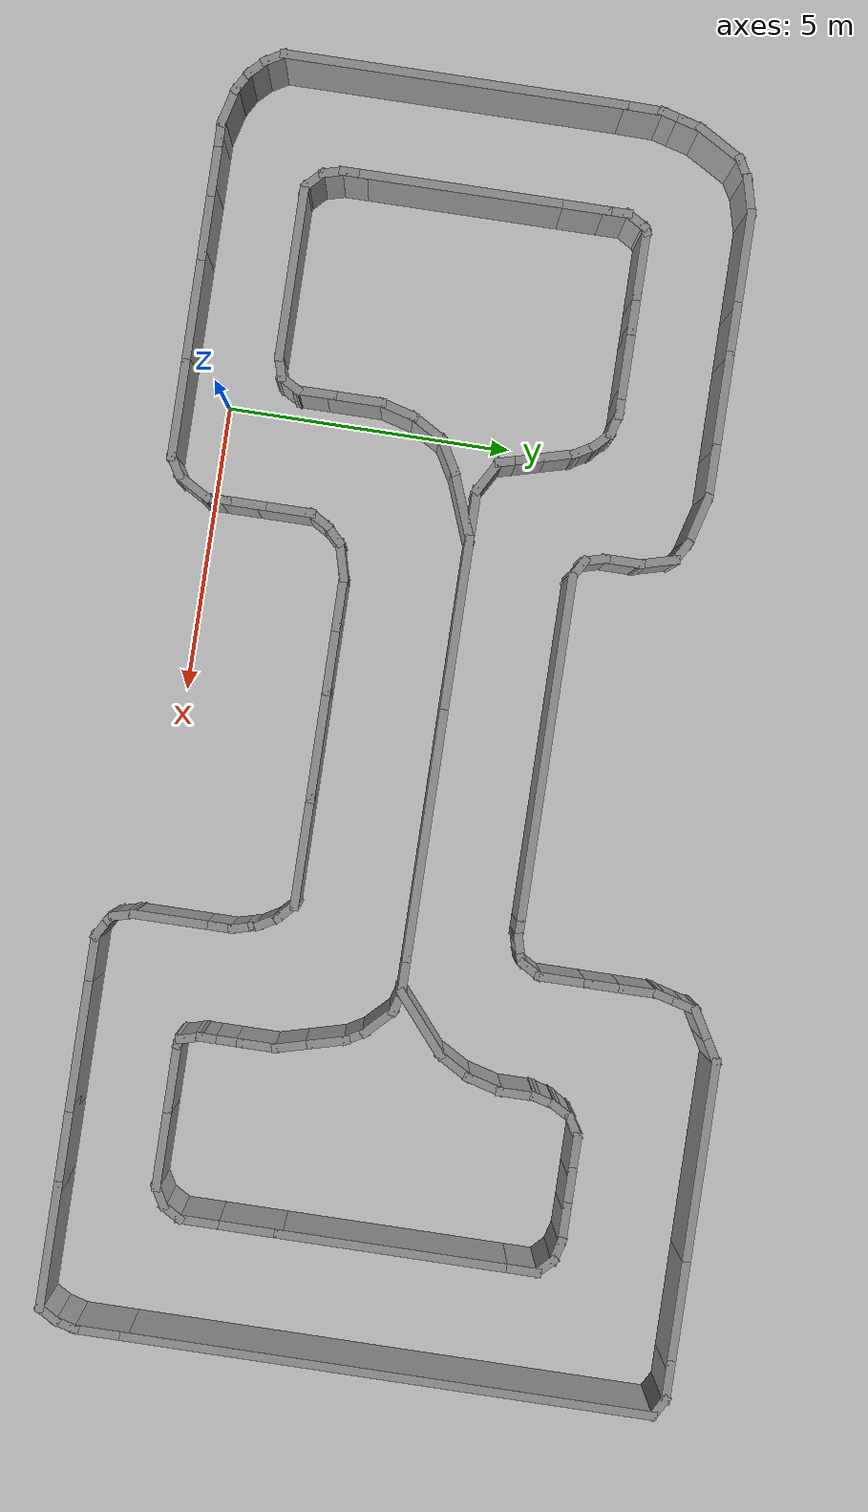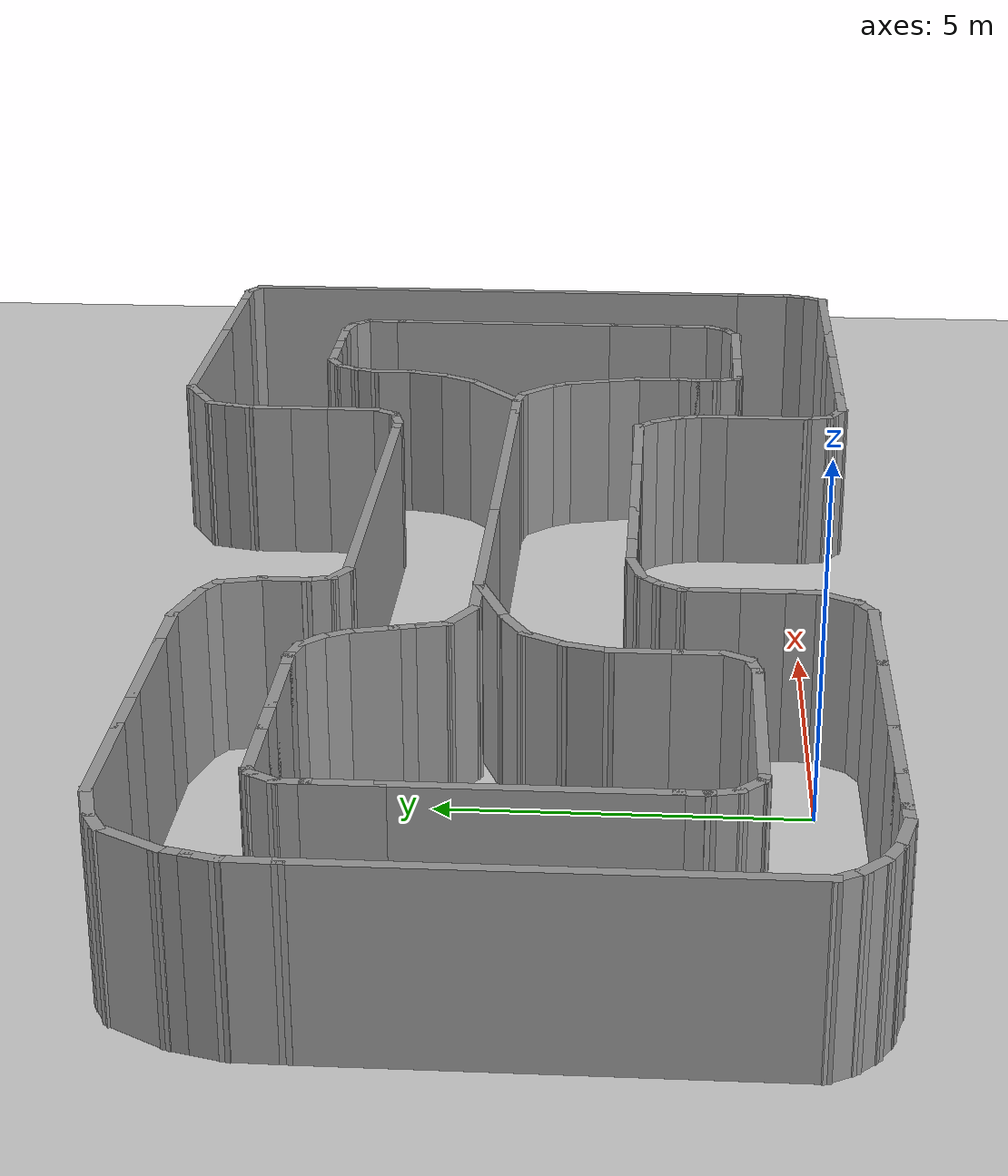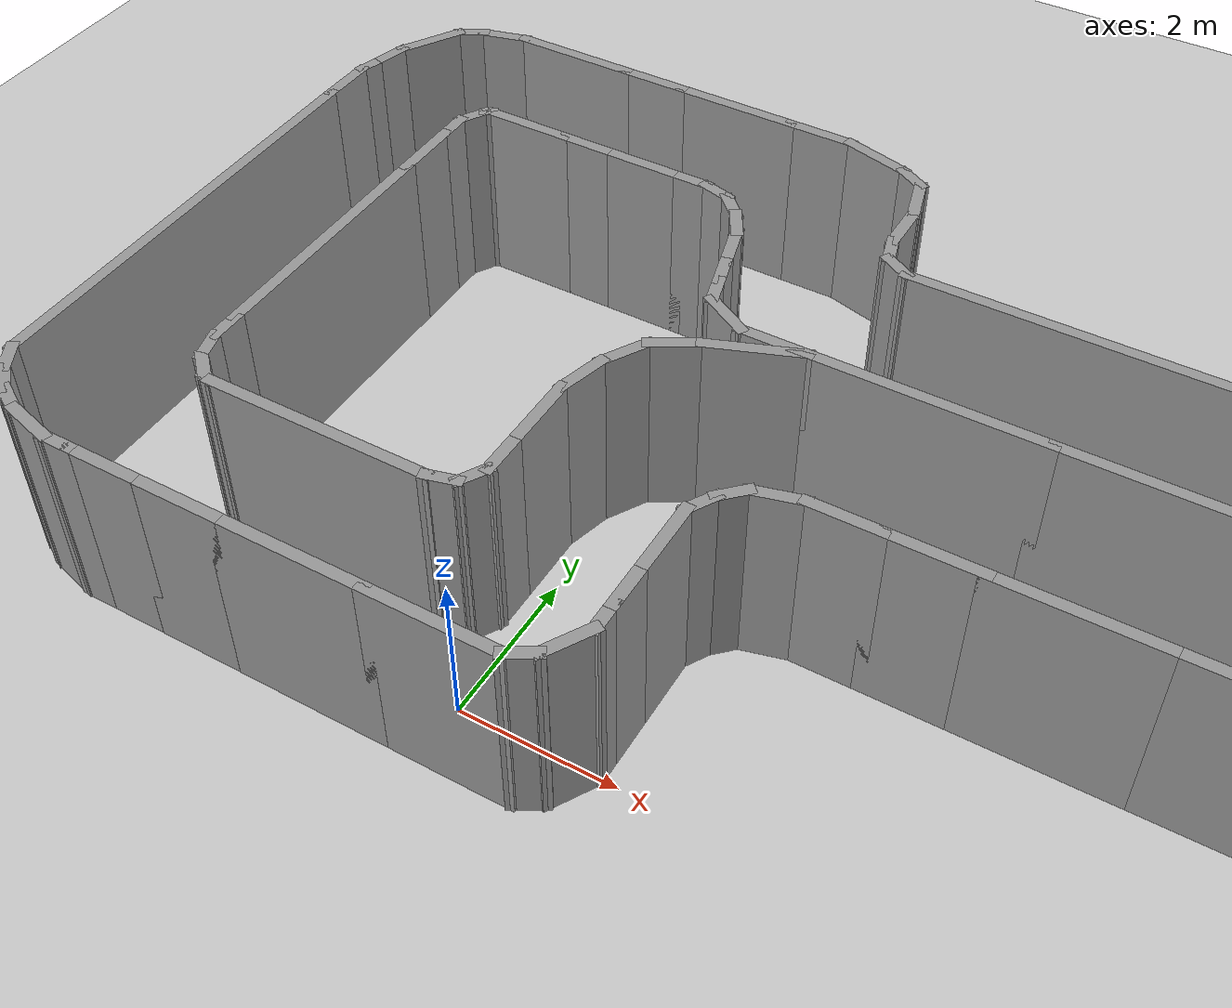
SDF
<sdf version="1.7">
 <world name="default">
  <light name="sun" type="directional">
   <pose>0 0 10 0 -0 0</pose>
   <diffuse>0.8 0.8 0.8 1</diffuse>
   <specular>0.2 0.2 0.2 1</specular>
   <attenuation>
    <range>1000</range>
    <constant>0.9</constant>
    <linear>0.01</linear>
    <quadratic>0.001</quadratic>
   </attenuation>
   <direction>-0.5 0.1 -0.9</direction>
   <spot><inner_angle>0</inner_angle><outer_angle>0</outer_angle><falloff>0</falloff></spot>
  </light>
  <model name="ground_plane">
   <static>1</static>
   <link name="link">
    <collision name="collision">
     <geometry><plane><normal>0 0 1</normal><size>100 100</size></plane></geometry>
     <surface><friction><ode><mu>100</mu><mu2>50</mu2></ode></friction></surface>
    </collision>
    <visual name="visual">
     <cast_shadows>0</cast_shadows>
     <geometry><plane><normal>0 0 1</normal><size>100 100</size></plane></geometry>
     <material>
      <script><uri>file://media/materials/scripts/gazebo.material</uri><name>Gazebo/Grey</name></script>
     </material>
    </visual>
   </link>
  </model>
  <gravity>0 0 -9.8</gravity>
  <magnetic_field>6e-06 2.3e-05 -4.2e-05</magnetic_field>
  <atmosphere type="adiabatic"/>
  <physics type="ode">
   <max_step_size>0.001</max_step_size>
   <real_time_factor>1</real_time_factor>
   <real_time_update_rate>1000</real_time_update_rate>
  </physics>
  <scene><ambient>0.4 0.4 0.4 1</ambient><background>0.7 0.7 0.7 1</background><shadows>1</shadows></scene>
  <audio><device>default</device></audio>
  <spherical_coordinates>
   <surface_model>EARTH_WGS84</surface_model>
   <latitude_deg>0</latitude_deg>
   <longitude_deg>0</longitude_deg>
   <elevation>0</elevation>
   <heading_deg>0</heading_deg>
  </spherical_coordinates>
  <model name="f1track">
   <pose>5.08169 4.60553 0 0 -0 0</pose>
   <link name="Wall_1">
    <collision name="Wall_1_Collision">
     <geometry><box><size>6 0.15 2.5</size></box></geometry>
     <pose>0 0 1.25 0 -0 0</pose>
    </collision>
    <visual name="Wall_1_Visual">
     <pose>0 0 1.25 0 -0 0</pose>
     <geometry><box><size>6 0.15 2.5</size></box></geometry>
     <material>
      <script><uri>file://media/materials/scripts/gazebo.material</uri><name>Gazebo/Grey</name></script>
      <ambient>1 1 1 1</ambient>
     </material>
     <meta><layer>0</layer></meta>
    </visual>
    <pose>-10.9896 -1.50866 0 0 -0 -1.5708</pose>
   </link>
   <link name="Wall_10">
    <collision name="Wall_10_Collision">
     <geometry><box><size>1.75 0.15 2.5</size></box></geometry>
     <pose>0 0 1.25 0 -0 0</pose>
    </collision>
    <visual name="Wall_10_Visual">
     <pose>0 0 1.25 0 -0 0</pose>
     <geometry><box><size>1.75 0.15 2.5</size></box></geometry>
     <material>
      <script><uri>file://media/materials/scripts/gazebo.material</uri><name>Gazebo/Grey</name></script>
      <ambient>1 1 1 1</ambient>
     </material>
     <meta><layer>0</layer></meta>
    </visual>
    <pose>-4.73447 -5.31455 0 0 -0 0</pose>
   </link>
   <link name="Wall_100">
    <collision name="Wall_100_Collision">
     <geometry><box><size>0.75 0.15 2.5</size></box></geometry>
     <pose>0 0 1.25 0 -0 0</pose>
    </collision>
    <visual name="Wall_100_Visual">
     <pose>0 0 1.25 0 -0 0</pose>
     <geometry><box><size>0.75 0.15 2.5</size></box></geometry>
     <material>
      <script><uri>file://media/materials/scripts/gazebo.material</uri><name>Gazebo/Grey</name></script>
      <ambient>1 1 1 1</ambient>
     </material>
     <meta><layer>0</layer></meta>
    </visual>
    <pose>5.52536 -1.1961 0 0 -0 -1.309</pose>
   </link>
   <link name="Wall_101">
    <collision name="Wall_101_Collision">
     <geometry><box><size>0.75 0.15 2.5</size></box></geometry>
     <pose>0 0 1.25 0 -0 0</pose>
    </collision>
    <visual name="Wall_101_Visual">
     <pose>0 0 1.25 0 -0 0</pose>
     <geometry><box><size>0.75 0.15 2.5</size></box></geometry>
     <material>
      <script><uri>file://media/materials/scripts/gazebo.material</uri><name>Gazebo/Grey</name></script>
      <ambient>1 1 1 1</ambient>
     </material>
     <meta><layer>0</layer></meta>
    </visual>
    <pose>5.68066 -1.77566 0 0 -0 -1.309</pose>
   </link>
   <link name="Wall_102">
    <collision name="Wall_102_Collision">
     <geometry><box><size>0.75 0.15 2.5</size></box></geometry>
     <pose>0 0 1.25 0 -0 0</pose>
    </collision>
    <visual name="Wall_102_Visual">
     <pose>0 0 1.25 0 -0 0</pose>
     <geometry><box><size>0.75 0.15 2.5</size></box></geometry>
     <material>
      <script><uri>file://media/materials/scripts/gazebo.material</uri><name>Gazebo/Grey</name></script>
      <ambient>1 1 1 1</ambient>
     </material>
     <meta><layer>0</layer></meta>
    </visual>
    <pose>5.7583 -2.36544 0 0 -0 -1.5708</pose>
   </link>
   <link name="Wall_103">
    <collision name="Wall_103_Collision">
     <geometry><box><size>0.5 0.15 2.5</size></box></geometry>
     <pose>0 0 1.25 0 -0 0</pose>
    </collision>
    <visual name="Wall_103_Visual">
     <pose>0 0 1.25 0 -0 0</pose>
     <geometry><box><size>0.5 0.15 2.5</size></box></geometry>
     <material>
      <script><uri>file://media/materials/scripts/gazebo.material</uri><name>Gazebo/Grey</name></script>
      <ambient>1 1 1 1</ambient>
     </material>
     <meta><layer>0</layer></meta>
    </visual>
    <pose>5.7583 -2.84044 0 0 -0 -1.5708</pose>
   </link>
   <link name="Wall_104">
    <collision name="Wall_104_Collision">
     <geometry><box><size>0.5 0.15 2.5</size></box></geometry>
     <pose>0 0 1.25 0 -0 0</pose>
    </collision>
    <visual name="Wall_104_Visual">
     <pose>0 0 1.25 0 -0 0</pose>
     <geometry><box><size>0.5 0.15 2.5</size></box></geometry>
     <material>
      <script><uri>file://media/materials/scripts/gazebo.material</uri><name>Gazebo/Grey</name></script>
      <ambient>1 1 1 1</ambient>
     </material>
     <meta><layer>0</layer></meta>
    </visual>
    <pose>5.7583 -3.19044 0 0 -0 -1.5708</pose>
   </link>
   <link name="Wall_105">
    <collision name="Wall_105_Collision">
     <geometry><box><size>0.5 0.15 2.5</size></box></geometry>
     <pose>0 0 1.25 0 -0 0</pose>
    </collision>
    <visual name="Wall_105_Visual">
     <pose>0 0 1.25 0 -0 0</pose>
     <geometry><box><size>0.5 0.15 2.5</size></box></geometry>
     <material>
      <script><uri>file://media/materials/scripts/gazebo.material</uri><name>Gazebo/Grey</name></script>
      <ambient>1 1 1 1</ambient>
     </material>
     <meta><layer>0</layer></meta>
    </visual>
    <pose>5.8036 -3.53448 0 0 -0 -1.309</pose>
   </link>
   <link name="Wall_106">
    <collision name="Wall_106_Collision">
     <geometry><box><size>0.25 0.15 2.5</size></box></geometry>
     <pose>0 0 1.25 0 -0 0</pose>
    </collision>
    <visual name="Wall_106_Visual">
     <pose>0 0 1.25 0 -0 0</pose>
     <geometry><box><size>0.25 0.15 2.5</size></box></geometry>
     <material>
      <script><uri>file://media/materials/scripts/gazebo.material</uri><name>Gazebo/Grey</name></script>
      <ambient>1 1 1 1</ambient>
     </material>
     <meta><layer>0</layer></meta>
    </visual>
    <pose>5.89718 -3.71645 0 0 -0 -0.261799</pose>
   </link>
   <link name="Wall_107">
    <collision name="Wall_107_Collision">
     <geometry><box><size>1.25 0.15 2.5</size></box></geometry>
     <pose>0 0 1.25 0 -0 0</pose>
    </collision>
    <visual name="Wall_107_Visual">
     <pose>0 0 1.25 0 -0 0</pose>
     <geometry><box><size>1.25 0.15 2.5</size></box></geometry>
     <material>
      <script><uri>file://media/materials/scripts/gazebo.material</uri><name>Gazebo/Grey</name></script>
      <ambient>1 1 1 1</ambient>
     </material>
     <meta><layer>0</layer></meta>
    </visual>
    <pose>6.49548 -3.72939 0 0 -0 0</pose>
   </link>
   <link name="Wall_108">
    <collision name="Wall_108_Collision">
     <geometry><box><size>1.5 0.15 2.5</size></box></geometry>
     <pose>0 0 1.25 0 -0 0</pose>
    </collision>
    <visual name="Wall_108_Visual">
     <pose>0 0 1.25 0 -0 0</pose>
     <geometry><box><size>1.5 0.15 2.5</size></box></geometry>
     <material>
      <script><uri>file://media/materials/scripts/gazebo.material</uri><name>Gazebo/Grey</name></script>
      <ambient>1 1 1 1</ambient>
     </material>
     <meta><layer>0</layer></meta>
    </visual>
    <pose>7.72048 -3.72939 0 0 -0 0</pose>
   </link>
   <link name="Wall_109">
    <collision name="Wall_109_Collision">
     <geometry><box><size>0.5 0.15 2.5</size></box></geometry>
     <pose>0 0 1.25 0 -0 0</pose>
    </collision>
    <visual name="Wall_109_Visual">
     <pose>0 0 1.25 0 -0 0</pose>
     <geometry><box><size>0.5 0.15 2.5</size></box></geometry>
     <material>
      <script><uri>file://media/materials/scripts/gazebo.material</uri><name>Gazebo/Grey</name></script>
      <ambient>1 1 1 1</ambient>
     </material>
     <meta><layer>0</layer></meta>
    </visual>
    <pose>8.54703 -3.64189 0 0 -0 0.523599</pose>
   </link>
   <link name="Wall_11">
    <collision name="Wall_11_Collision">
     <geometry><box><size>0.5 0.15 2.5</size></box></geometry>
     <pose>0 0 1.25 0 -0 0</pose>
    </collision>
    <visual name="Wall_11_Visual">
     <pose>0 0 1.25 0 -0 0</pose>
     <geometry><box><size>0.5 0.15 2.5</size></box></geometry>
     <material>
      <script><uri>file://media/materials/scripts/gazebo.material</uri><name>Gazebo/Grey</name></script>
      <ambient>1 1 1 1</ambient>
     </material>
     <meta><layer>0</layer></meta>
    </visual>
    <pose>-3.78292 -5.22705 0 0 -0 0.523599</pose>
   </link>
   <link name="Wall_110">
    <collision name="Wall_110_Collision">
     <geometry><box><size>0.5 0.15 2.5</size></box></geometry>
     <pose>0 0 1.25 0 -0 0</pose>
    </collision>
    <visual name="Wall_110_Visual">
     <pose>0 0 1.25 0 -0 0</pose>
     <geometry><box><size>0.5 0.15 2.5</size></box></geometry>
     <material>
      <script><uri>file://media/materials/scripts/gazebo.material</uri><name>Gazebo/Grey</name></script>
      <ambient>1 1 1 1</ambient>
     </material>
     <meta><layer>0</layer></meta>
    </visual>
    <pose>8.78609 -3.40284 0 0 -0 1.0472</pose>
   </link>
   <link name="Wall_111">
    <collision name="Wall_111_Collision">
     <geometry><box><size>0.75 0.15 2.5</size></box></geometry>
     <pose>0 0 1.25 0 -0 0</pose>
    </collision>
    <visual name="Wall_111_Visual">
     <pose>0 0 1.25 0 -0 0</pose>
     <geometry><box><size>0.75 0.15 2.5</size></box></geometry>
     <material>
      <script><uri>file://media/materials/scripts/gazebo.material</uri><name>Gazebo/Grey</name></script>
      <ambient>1 1 1 1</ambient>
     </material>
     <meta><layer>0</layer></meta>
    </visual>
    <pose>8.87359 -2.95128 0 0 -0 1.5708</pose>
   </link>
   <link name="Wall_112">
    <collision name="Wall_112_Collision">
     <geometry><box><size>1.25 0.15 2.5</size></box></geometry>
     <pose>0 0 1.25 0 -0 0</pose>
    </collision>
    <visual name="Wall_112_Visual">
     <pose>0 0 1.25 0 -0 0</pose>
     <geometry><box><size>1.25 0.15 2.5</size></box></geometry>
     <material>
      <script><uri>file://media/materials/scripts/gazebo.material</uri><name>Gazebo/Grey</name></script>
      <ambient>1 1 1 1</ambient>
     </material>
     <meta><layer>0</layer></meta>
    </visual>
    <pose>8.87359 -2.10128 0 0 -0 1.5708</pose>
   </link>
   <link name="Wall_113">
    <collision name="Wall_113_Collision">
     <geometry><box><size>4 0.15 2.5</size></box></geometry>
     <pose>0 0 1.25 0 -0 0</pose>
    </collision>
    <visual name="Wall_113_Visual">
     <pose>0 0 1.25 0 -0 0</pose>
     <geometry><box><size>4 0.15 2.5</size></box></geometry>
     <material>
      <script><uri>file://media/materials/scripts/gazebo.material</uri><name>Gazebo/Grey</name></script>
      <ambient>1 1 1 1</ambient>
     </material>
     <meta><layer>0</layer></meta>
    </visual>
    <pose>8.87359 0.373715 0 0 -0 1.5708</pose>
   </link>
   <link name="Wall_114">
    <collision name="Wall_114_Collision">
     <geometry><box><size>0.75 0.15 2.5</size></box></geometry>
     <pose>0 0 1.25 0 -0 0</pose>
    </collision>
    <visual name="Wall_114_Visual">
     <pose>0 0 1.25 0 -0 0</pose>
     <geometry><box><size>0.75 0.15 2.5</size></box></geometry>
     <material>
      <script><uri>file://media/materials/scripts/gazebo.material</uri><name>Gazebo/Grey</name></script>
      <ambient>1 1 1 1</ambient>
     </material>
     <meta><layer>0</layer></meta>
    </visual>
    <pose>8.87359 2.59871 0 0 -0 1.5708</pose>
   </link>
   <link name="Wall_115">
    <collision name="Wall_115_Collision">
     <geometry><box><size>0.5 0.15 2.5</size></box></geometry>
     <pose>0 0 1.25 0 -0 0</pose>
    </collision>
    <visual name="Wall_115_Visual">
     <pose>0 0 1.25 0 -0 0</pose>
     <geometry><box><size>0.5 0.15 2.5</size></box></geometry>
     <material>
      <script><uri>file://media/materials/scripts/gazebo.material</uri><name>Gazebo/Grey</name></script>
      <ambient>1 1 1 1</ambient>
     </material>
     <meta><layer>0</layer></meta>
    </visual>
    <pose>8.74985 3.02246 0 0 -0 2.35619</pose>
   </link>
   <link name="Wall_116">
    <collision name="Wall_116_Collision">
     <geometry><box><size>0.5 0.15 2.5</size></box></geometry>
     <pose>0 0 1.25 0 -0 0</pose>
    </collision>
    <visual name="Wall_116_Visual">
     <pose>0 0 1.25 0 -0 0</pose>
     <geometry><box><size>0.5 0.15 2.5</size></box></geometry>
     <material>
      <script><uri>file://media/materials/scripts/gazebo.material</uri><name>Gazebo/Grey</name></script>
      <ambient>1 1 1 1</ambient>
     </material>
     <meta><layer>0</layer></meta>
    </visual>
    <pose>8.45707 3.1915 0 0 -0 2.87979</pose>
   </link>
   <link name="Wall_117">
    <collision name="Wall_117_Collision">
     <geometry><box><size>0.75 0.15 2.5</size></box></geometry>
     <pose>0 0 1.25 0 -0 0</pose>
    </collision>
    <visual name="Wall_117_Visual">
     <pose>0 0 1.25 0 -0 0</pose>
     <geometry><box><size>0.75 0.15 2.5</size></box></geometry>
     <material>
      <script><uri>file://media/materials/scripts/gazebo.material</uri><name>Gazebo/Grey</name></script>
      <ambient>1 1 1 1</ambient>
     </material>
     <meta><layer>0</layer></meta>
    </visual>
    <pose>7.98803 3.23679 0 0 -0 3.14159</pose>
   </link>
   <link name="Wall_118">
    <collision name="Wall_118_Collision">
     <geometry><box><size>0.75 0.15 2.5</size></box></geometry>
     <pose>0 0 1.25 0 -0 0</pose>
    </collision>
    <visual name="Wall_118_Visual">
     <pose>0 0 1.25 0 -0 0</pose>
     <geometry><box><size>0.75 0.15 2.5</size></box></geometry>
     <material>
      <script><uri>file://media/materials/scripts/gazebo.material</uri><name>Gazebo/Grey</name></script>
      <ambient>1 1 1 1</ambient>
     </material>
     <meta><layer>0</layer></meta>
    </visual>
    <pose>7.38803 3.23679 0 0 -0 3.14159</pose>
   </link>
   <link name="Wall_12">
    <collision name="Wall_12_Collision">
     <geometry><box><size>0.75 0.15 2.5</size></box></geometry>
     <pose>0 0 1.25 0 -0 0</pose>
    </collision>
    <visual name="Wall_12_Visual">
     <pose>0 0 1.25 0 -0 0</pose>
     <geometry><box><size>0.75 0.15 2.5</size></box></geometry>
     <material>
      <script><uri>file://media/materials/scripts/gazebo.material</uri><name>Gazebo/Grey</name></script>
      <ambient>1 1 1 1</ambient>
     </material>
     <meta><layer>0</layer></meta>
    </visual>
    <pose>-3.48137 -4.87974 0 0 -0 1.0472</pose>
   </link>
   <link name="Wall_121">
    <collision name="Wall_121_Collision">
     <geometry><box><size>0.75 0.15 2.5</size></box></geometry>
     <pose>0 0 1.25 0 -0 0</pose>
    </collision>
    <visual name="Wall_121_Visual">
     <pose>0 0 1.25 0 -0 0</pose>
     <geometry><box><size>0.75 0.15 2.5</size></box></geometry>
     <material>
      <script><uri>file://media/materials/scripts/gazebo.material</uri><name>Gazebo/Grey</name></script>
      <ambient>1 1 1 1</ambient>
     </material>
     <meta><layer>0</layer></meta>
    </visual>
    <pose>6.78803 3.23679 0 0 -0 3.14159</pose>
   </link>
   <link name="Wall_122">
    <collision name="Wall_122_Collision">
     <geometry><box><size>0.5 0.15 2.5</size></box></geometry>
     <pose>0 0 1.25 0 -0 0</pose>
    </collision>
    <visual name="Wall_122_Visual">
     <pose>0 0 1.25 0 -0 0</pose>
     <geometry><box><size>0.5 0.15 2.5</size></box></geometry>
     <material>
      <script><uri>file://media/materials/scripts/gazebo.material</uri><name>Gazebo/Grey</name></script>
      <ambient>1 1 1 1</ambient>
     </material>
     <meta><layer>0</layer></meta>
    </visual>
    <pose>6.33647 3.14929 0 0 -0 -2.61799</pose>
   </link>
   <link name="Wall_123">
    <collision name="Wall_123_Collision">
     <geometry><box><size>0.5 0.15 2.5</size></box></geometry>
     <pose>0 0 1.25 0 -0 0</pose>
    </collision>
    <visual name="Wall_123_Visual">
     <pose>0 0 1.25 0 -0 0</pose>
     <geometry><box><size>0.5 0.15 2.5</size></box></geometry>
     <material>
      <script><uri>file://media/materials/scripts/gazebo.material</uri><name>Gazebo/Grey</name></script>
      <ambient>1 1 1 1</ambient>
     </material>
     <meta><layer>0</layer></meta>
    </visual>
    <pose>6.09742 2.91024 0 0 -0 -2.0944</pose>
   </link>
   <link name="Wall_124">
    <collision name="Wall_124_Collision">
     <geometry><box><size>0.5 0.15 2.5</size></box></geometry>
     <pose>0 0 1.25 0 -0 0</pose>
    </collision>
    <visual name="Wall_124_Visual">
     <pose>0 0 1.25 0 -0 0</pose>
     <geometry><box><size>0.5 0.15 2.5</size></box></geometry>
     <material>
      <script><uri>file://media/materials/scripts/gazebo.material</uri><name>Gazebo/Grey</name></script>
      <ambient>1 1 1 1</ambient>
     </material>
     <meta><layer>0</layer></meta>
    </visual>
    <pose>5.96463 2.58964 0 0 -0 -1.8326</pose>
   </link>
   <link name="Wall_125">
    <collision name="Wall_125_Collision">
     <geometry><box><size>0.75 0.15 2.5</size></box></geometry>
     <pose>0 0 1.25 0 -0 0</pose>
    </collision>
    <visual name="Wall_125_Visual">
     <pose>0 0 1.25 0 -0 0</pose>
     <geometry><box><size>0.75 0.15 2.5</size></box></geometry>
     <material>
      <script><uri>file://media/materials/scripts/gazebo.material</uri><name>Gazebo/Grey</name></script>
      <ambient>1 1 1 1</ambient>
     </material>
     <meta><layer>0</layer></meta>
    </visual>
    <pose>5.91933 2.12061 0 0 -0 -1.5708</pose>
   </link>
   <link name="Wall_126">
    <collision name="Wall_126_Collision">
     <geometry><box><size>0.75 0.15 2.5</size></box></geometry>
     <pose>0 0 1.25 0 -0 0</pose>
    </collision>
    <visual name="Wall_126_Visual">
     <pose>0 0 1.25 0 -0 0</pose>
     <geometry><box><size>0.75 0.15 2.5</size></box></geometry>
     <material>
      <script><uri>file://media/materials/scripts/gazebo.material</uri><name>Gazebo/Grey</name></script>
      <ambient>1 1 1 1</ambient>
     </material>
     <meta><layer>0</layer></meta>
    </visual>
    <pose>5.84169 1.53083 0 0 -0 -1.8326</pose>
   </link>
   <link name="Wall_127">
    <collision name="Wall_127_Collision">
     <geometry><box><size>0.75 0.15 2.5</size></box></geometry>
     <pose>0 0 1.25 0 -0 0</pose>
    </collision>
    <visual name="Wall_127_Visual">
     <pose>0 0 1.25 0 -0 0</pose>
     <geometry><box><size>0.75 0.15 2.5</size></box></geometry>
     <material>
      <script><uri>file://media/materials/scripts/gazebo.material</uri><name>Gazebo/Grey</name></script>
      <ambient>1 1 1 1</ambient>
     </material>
     <meta><layer>0</layer></meta>
    </visual>
    <pose>5.61404 0.981243 0 0 -0 -2.0944</pose>
   </link>
   <link name="Wall_128">
    <collision name="Wall_128_Collision">
     <geometry><box><size>1.4011 0.15 2.5</size></box></geometry>
     <pose>0 0 1.25 0 -0 0</pose>
    </collision>
    <visual name="Wall_128_Visual">
     <pose>0 0 1.25 0 -0 0</pose>
     <geometry><box><size>1.4011 0.15 2.5</size></box></geometry>
     <material>
      <script><uri>file://media/materials/scripts/gazebo.material</uri><name>Gazebo/Grey</name></script>
      <ambient>1 1 1 1</ambient>
     </material>
     <meta><layer>0</layer></meta>
    </visual>
    <pose>4.98721 0.316534 0 0 -0 -2.43759</pose>
   </link>
   <link name="Wall_13">
    <collision name="Wall_13_Collision">
     <geometry><box><size>0.5 0.15 2.5</size></box></geometry>
     <pose>0 0 1.25 0 -0 0</pose>
    </collision>
    <visual name="Wall_13_Visual">
     <pose>0 0 1.25 0 -0 0</pose>
     <geometry><box><size>0.5 0.15 2.5</size></box></geometry>
     <material>
      <script><uri>file://media/materials/scripts/gazebo.material</uri><name>Gazebo/Grey</name></script>
      <ambient>1 1 1 1</ambient>
     </material>
     <meta><layer>0</layer></meta>
    </visual>
    <pose>-3.33137 -4.44493 0 0 -0 1.5708</pose>
   </link>
   <link name="Wall_131">
    <collision name="Wall_131_Collision">
     <geometry><box><size>3.5 0.15 2.5</size></box></geometry>
     <pose>0 0 1.25 0 -0 0</pose>
    </collision>
    <visual name="Wall_131_Visual">
     <pose>0 0 1.25 0 -0 0</pose>
     <geometry><box><size>3.5 0.15 2.5</size></box></geometry>
     <material>
      <script><uri>file://media/materials/scripts/gazebo.material</uri><name>Gazebo/Grey</name></script>
      <ambient>1 1 1 1</ambient>
     </material>
     <meta><layer>0</layer></meta>
    </visual>
    <pose>-9.16786 -1.11959 0 0 -0 -1.5708</pose>
   </link>
   <link name="Wall_132">
    <collision name="Wall_132_Collision">
     <geometry><box><size>0.5 0.15 2.5</size></box></geometry>
     <pose>0 0 1.25 0 -0 0</pose>
    </collision>
    <visual name="Wall_132_Visual">
     <pose>0 0 1.25 0 -0 0</pose>
     <geometry><box><size>0.5 0.15 2.5</size></box></geometry>
     <material>
      <script><uri>file://media/materials/scripts/gazebo.material</uri><name>Gazebo/Grey</name></script>
      <ambient>1 1 1 1</ambient>
     </material>
     <meta><layer>0</layer></meta>
    </visual>
    <pose>-9.16786 -2.96959 0 0 -0 -1.5708</pose>
   </link>
   <link name="Wall_133">
    <collision name="Wall_133_Collision">
     <geometry><box><size>0.5 0.15 2.5</size></box></geometry>
     <pose>0 0 1.25 0 -0 0</pose>
    </collision>
    <visual name="Wall_133_Visual">
     <pose>0 0 1.25 0 -0 0</pose>
     <geometry><box><size>0.5 0.15 2.5</size></box></geometry>
     <material>
      <script><uri>file://media/materials/scripts/gazebo.material</uri><name>Gazebo/Grey</name></script>
      <ambient>1 1 1 1</ambient>
     </material>
     <meta><layer>0</layer></meta>
    </visual>
    <pose>-9.12257 -3.31363 0 0 -0 -1.309</pose>
   </link>
   <link name="Wall_134">
    <collision name="Wall_134_Collision">
     <geometry><box><size>0.5 0.15 2.5</size></box></geometry>
     <pose>0 0 1.25 0 -0 0</pose>
    </collision>
    <visual name="Wall_134_Visual">
     <pose>0 0 1.25 0 -0 0</pose>
     <geometry><box><size>0.5 0.15 2.5</size></box></geometry>
     <material>
      <script><uri>file://media/materials/scripts/gazebo.material</uri><name>Gazebo/Grey</name></script>
      <ambient>1 1 1 1</ambient>
     </material>
     <meta><layer>0</layer></meta>
    </visual>
    <pose>-8.95353 -3.60641 0 0 -0 -0.785398</pose>
   </link>
   <link name="Wall_135">
    <collision name="Wall_135_Collision">
     <geometry><box><size>0.25 0.15 2.5</size></box></geometry>
     <pose>0 0 1.25 0 -0 0</pose>
    </collision>
    <visual name="Wall_135_Visual">
     <pose>0 0 1.25 0 -0 0</pose>
     <geometry><box><size>0.25 0.15 2.5</size></box></geometry>
     <material>
      <script><uri>file://media/materials/scripts/gazebo.material</uri><name>Gazebo/Grey</name></script>
      <ambient>1 1 1 1</ambient>
     </material>
     <meta><layer>0</layer></meta>
    </visual>
    <pose>-8.78149 -3.74309 0 0 -0 -0.261799</pose>
   </link>
   <link name="Wall_136">
    <collision name="Wall_136_Collision">
     <geometry><box><size>3 0.15 2.5</size></box></geometry>
     <pose>0 0 1.25 0 -0 0</pose>
    </collision>
    <visual name="Wall_136_Visual">
     <pose>0 0 1.25 0 -0 0</pose>
     <geometry><box><size>3 0.15 2.5</size></box></geometry>
     <material>
      <script><uri>file://media/materials/scripts/gazebo.material</uri><name>Gazebo/Grey</name></script>
      <ambient>1 1 1 1</ambient>
     </material>
     <meta><layer>0</layer></meta>
    </visual>
    <pose>-7.3082 -3.75603 0 0 -0 0</pose>
   </link>
   <link name="Wall_137">
    <collision name="Wall_137_Collision">
     <geometry><box><size>0.5 0.15 2.5</size></box></geometry>
     <pose>0 0 1.25 0 -0 0</pose>
    </collision>
    <visual name="Wall_137_Visual">
     <pose>0 0 1.25 0 -0 0</pose>
     <geometry><box><size>0.5 0.15 2.5</size></box></geometry>
     <material>
      <script><uri>file://media/materials/scripts/gazebo.material</uri><name>Gazebo/Grey</name></script>
      <ambient>1 1 1 1</ambient>
     </material>
     <meta><layer>0</layer></meta>
    </visual>
    <pose>-5.71416 -3.71074 0 0 -0 0.261799</pose>
   </link>
   <link name="Wall_138">
    <collision name="Wall_138_Collision">
     <geometry><box><size>0.5 0.15 2.5</size></box></geometry>
     <pose>0 0 1.25 0 -0 0</pose>
    </collision>
    <visual name="Wall_138_Visual">
     <pose>0 0 1.25 0 -0 0</pose>
     <geometry><box><size>0.5 0.15 2.5</size></box></geometry>
     <material>
      <script><uri>file://media/materials/scripts/gazebo.material</uri><name>Gazebo/Grey</name></script>
      <ambient>1 1 1 1</ambient>
     </material>
     <meta><layer>0</layer></meta>
    </visual>
    <pose>-5.45762 -3.51389 0 0 -0 1.0472</pose>
   </link>
   <link name="Wall_139">
    <collision name="Wall_139_Collision">
     <geometry><box><size>0.75 0.15 2.5</size></box></geometry>
     <pose>0 0 1.25 0 -0 0</pose>
    </collision>
    <visual name="Wall_139_Visual">
     <pose>0 0 1.25 0 -0 0</pose>
     <geometry><box><size>0.75 0.15 2.5</size></box></geometry>
     <material>
      <script><uri>file://media/materials/scripts/gazebo.material</uri><name>Gazebo/Grey</name></script>
      <ambient>1 1 1 1</ambient>
     </material>
     <meta><layer>0</layer></meta>
    </visual>
    <pose>-5.37012 -3.06234 0 0 -0 1.5708</pose>
   </link>
   <link name="Wall_14">
    <collision name="Wall_14_Collision">
     <geometry><box><size>0.75 0.15 2.5</size></box></geometry>
     <pose>0 0 1.25 0 -0 0</pose>
    </collision>
    <visual name="Wall_14_Visual">
     <pose>0 0 1.25 0 -0 0</pose>
     <geometry><box><size>0.75 0.15 2.5</size></box></geometry>
     <material>
      <script><uri>file://media/materials/scripts/gazebo.material</uri><name>Gazebo/Grey</name></script>
      <ambient>1 1 1 1</ambient>
     </material>
     <meta><layer>0</layer></meta>
    </visual>
    <pose>-3.33137 -3.96993 0 0 -0 1.5708</pose>
   </link>
   <link name="Wall_140">
    <collision name="Wall_140_Collision">
     <geometry><box><size>1 0.15 2.5</size></box></geometry>
     <pose>0 0 1.25 0 -0 0</pose>
    </collision>
    <visual name="Wall_140_Visual">
     <pose>0 0 1.25 0 -0 0</pose>
     <geometry><box><size>1 0.15 2.5</size></box></geometry>
     <material>
      <script><uri>file://media/materials/scripts/gazebo.material</uri><name>Gazebo/Grey</name></script>
      <ambient>1 1 1 1</ambient>
     </material>
     <meta><layer>0</layer></meta>
    </visual>
    <pose>-5.37012 -2.33734 0 0 -0 1.5708</pose>
   </link>
   <link name="Wall_141">
    <collision name="Wall_141_Collision">
     <geometry><box><size>0.75 0.15 2.5</size></box></geometry>
     <pose>0 0 1.25 0 -0 0</pose>
    </collision>
    <visual name="Wall_141_Visual">
     <pose>0 0 1.25 0 -0 0</pose>
     <geometry><box><size>0.75 0.15 2.5</size></box></geometry>
     <material>
      <script><uri>file://media/materials/scripts/gazebo.material</uri><name>Gazebo/Grey</name></script>
      <ambient>1 1 1 1</ambient>
     </material>
     <meta><layer>0</layer></meta>
    </visual>
    <pose>-5.29248 -1.62256 0 0 -0 1.309</pose>
   </link>
   <link name="Wall_142">
    <collision name="Wall_142_Collision">
     <geometry><box><size>0.75 0.15 2.5</size></box></geometry>
     <pose>0 0 1.25 0 -0 0</pose>
    </collision>
    <visual name="Wall_142_Visual">
     <pose>0 0 1.25 0 -0 0</pose>
     <geometry><box><size>0.75 0.15 2.5</size></box></geometry>
     <material>
      <script><uri>file://media/materials/scripts/gazebo.material</uri><name>Gazebo/Grey</name></script>
      <ambient>1 1 1 1</ambient>
     </material>
     <meta><layer>0</layer></meta>
    </visual>
    <pose>-5.06483 -1.07297 0 0 -0 1.0472</pose>
   </link>
   <link name="Wall_143">
    <collision name="Wall_143_Collision">
     <geometry><box><size>0.75 0.15 2.5</size></box></geometry>
     <pose>0 0 1.25 0 -0 0</pose>
    </collision>
    <visual name="Wall_143_Visual">
     <pose>0 0 1.25 0 -0 0</pose>
     <geometry><box><size>0.75 0.15 2.5</size></box></geometry>
     <material>
      <script><uri>file://media/materials/scripts/gazebo.material</uri><name>Gazebo/Grey</name></script>
      <ambient>1 1 1 1</ambient>
     </material>
     <meta><layer>0</layer></meta>
    </visual>
    <pose>-4.65502 -0.663167 0 0 -0 0.523599</pose>
   </link>
   <link name="Wall_146">
    <collision name="Wall_146_Collision">
     <geometry><box><size>1.3344 0.15 2.5</size></box></geometry>
     <pose>0 0 1.25 0 -0 0</pose>
    </collision>
    <visual name="Wall_146_Visual">
     <pose>0 0 1.25 0 -0 0</pose>
     <geometry><box><size>1.3344 0.15 2.5</size></box></geometry>
     <material>
      <script><uri>file://media/materials/scripts/gazebo.material</uri><name>Gazebo/Grey</name></script>
      <ambient>1 1 1 1</ambient>
     </material>
     <meta><layer>0</layer></meta>
    </visual>
    <pose>-3.84242 -0.300767 0 0 -0 0.366835</pose>
   </link>
   <link name="Wall_15">
    <collision name="Wall_15_Collision">
     <geometry><box><size>1 0.15 2.5</size></box></geometry>
     <pose>0 0 1.25 0 -0 0</pose>
    </collision>
    <visual name="Wall_15_Visual">
     <pose>0 0 1.25 0 -0 0</pose>
     <geometry><box><size>1 0.15 2.5</size></box></geometry>
     <material>
      <script><uri>file://media/materials/scripts/gazebo.material</uri><name>Gazebo/Grey</name></script>
      <ambient>1 1 1 1</ambient>
     </material>
     <meta><layer>0</layer></meta>
    </visual>
    <pose>-3.33137 -3.24493 0 0 -0 1.5708</pose>
   </link>
   <link name="Wall_16">
    <collision name="Wall_16_Collision">
     <geometry><box><size>0.5 0.15 2.5</size></box></geometry>
     <pose>0 0 1.25 0 -0 0</pose>
    </collision>
    <visual name="Wall_16_Visual">
     <pose>0 0 1.25 0 -0 0</pose>
     <geometry><box><size>0.5 0.15 2.5</size></box></geometry>
     <material>
      <script><uri>file://media/materials/scripts/gazebo.material</uri><name>Gazebo/Grey</name></script>
      <ambient>1 1 1 1</ambient>
     </material>
     <meta><layer>0</layer></meta>
    </visual>
    <pose>-3.24387 -2.66838 0 0 -0 1.0472</pose>
   </link>
   <link name="Wall_17">
    <collision name="Wall_17_Collision">
     <geometry><box><size>0.5 0.15 2.5</size></box></geometry>
     <pose>0 0 1.25 0 -0 0</pose>
    </collision>
    <visual name="Wall_17_Visual">
     <pose>0 0 1.25 0 -0 0</pose>
     <geometry><box><size>0.5 0.15 2.5</size></box></geometry>
     <material>
      <script><uri>file://media/materials/scripts/gazebo.material</uri><name>Gazebo/Grey</name></script>
      <ambient>1 1 1 1</ambient>
     </material>
     <meta><layer>0</layer></meta>
    </visual>
    <pose>-3.03262 -2.39308 0 0 -0 0.785398</pose>
   </link>
   <link name="Wall_18">
    <collision name="Wall_18_Collision">
     <geometry><box><size>0.75 0.15 2.5</size></box></geometry>
     <pose>0 0 1.25 0 -0 0</pose>
    </collision>
    <visual name="Wall_18_Visual">
     <pose>0 0 1.25 0 -0 0</pose>
     <geometry><box><size>0.75 0.15 2.5</size></box></geometry>
     <material>
      <script><uri>file://media/materials/scripts/gazebo.material</uri><name>Gazebo/Grey</name></script>
      <ambient>1 1 1 1</ambient>
     </material>
     <meta><layer>0</layer></meta>
    </visual>
    <pose>-2.6191 -2.19169 0 0 -0 0.261799</pose>
   </link>
   <link name="Wall_19">
    <collision name="Wall_19_Collision">
     <geometry><box><size>1 0.15 2.5</size></box></geometry>
     <pose>0 0 1.25 0 -0 0</pose>
    </collision>
    <visual name="Wall_19_Visual">
     <pose>0 0 1.25 0 -0 0</pose>
     <geometry><box><size>1 0.15 2.5</size></box></geometry>
     <material>
      <script><uri>file://media/materials/scripts/gazebo.material</uri><name>Gazebo/Grey</name></script>
      <ambient>1 1 1 1</ambient>
     </material>
     <meta><layer>0</layer></meta>
    </visual>
    <pose>-1.90432 -2.11404 0 0 -0 0</pose>
   </link>
   <link name="Wall_2">
    <collision name="Wall_2_Collision">
     <geometry><box><size>0.5 0.15 2.5</size></box></geometry>
     <pose>0 0 1.25 0 -0 0</pose>
    </collision>
    <visual name="Wall_2_Visual">
     <pose>0 0 1.25 0 -0 0</pose>
     <geometry><box><size>0.5 0.15 2.5</size></box></geometry>
     <material>
      <script><uri>file://media/materials/scripts/gazebo.material</uri><name>Gazebo/Grey</name></script>
      <ambient>1 1 1 1</ambient>
     </material>
     <meta><layer>0</layer></meta>
    </visual>
    <pose>-10.9021 -4.58521 0 0 -0 -1.0472</pose>
   </link>
   <link name="Wall_20">
    <collision name="Wall_20_Collision">
     <geometry><box><size>1.25 0.15 2.5</size></box></geometry>
     <pose>0 0 1.25 0 -0 0</pose>
    </collision>
    <visual name="Wall_20_Visual">
     <pose>0 0 1.25 0 -0 0</pose>
     <geometry><box><size>1.25 0.15 2.5</size></box></geometry>
     <material>
      <script><uri>file://media/materials/scripts/gazebo.material</uri><name>Gazebo/Grey</name></script>
      <ambient>1 1 1 1</ambient>
     </material>
     <meta><layer>0</layer></meta>
    </visual>
    <pose>-0.929323 -2.11404 0 0 -0 0</pose>
   </link>
   <link name="Wall_21">
    <collision name="Wall_21_Collision">
     <geometry><box><size>2 0.15 2.5</size></box></geometry>
     <pose>0 0 1.25 0 -0 0</pose>
    </collision>
    <visual name="Wall_21_Visual">
     <pose>0 0 1.25 0 -0 0</pose>
     <geometry><box><size>2 0.15 2.5</size></box></geometry>
     <material>
      <script><uri>file://media/materials/scripts/gazebo.material</uri><name>Gazebo/Grey</name></script>
      <ambient>1 1 1 1</ambient>
     </material>
     <meta><layer>0</layer></meta>
    </visual>
    <pose>0.545677 -2.11404 0 0 -0 0</pose>
   </link>
   <link name="Wall_22">
    <collision name="Wall_22_Collision">
     <geometry><box><size>2 0.15 2.5</size></box></geometry>
     <pose>0 0 1.25 0 -0 0</pose>
    </collision>
    <visual name="Wall_22_Visual">
     <pose>0 0 1.25 0 -0 0</pose>
     <geometry><box><size>2 0.15 2.5</size></box></geometry>
     <material>
      <script><uri>file://media/materials/scripts/gazebo.material</uri><name>Gazebo/Grey</name></script>
      <ambient>1 1 1 1</ambient>
     </material>
     <meta><layer>0</layer></meta>
    </visual>
    <pose>2.39568 -2.11404 0 0 -0 0</pose>
   </link>
   <link name="Wall_23">
    <collision name="Wall_23_Collision">
     <geometry><box><size>0.5 0.15 2.5</size></box></geometry>
     <pose>0 0 1.25 0 -0 0</pose>
    </collision>
    <visual name="Wall_23_Visual">
     <pose>0 0 1.25 0 -0 0</pose>
     <geometry><box><size>0.5 0.15 2.5</size></box></geometry>
     <material>
      <script><uri>file://media/materials/scripts/gazebo.material</uri><name>Gazebo/Grey</name></script>
      <ambient>1 1 1 1</ambient>
     </material>
     <meta><layer>0</layer></meta>
    </visual>
    <pose>3.44442 -2.23779 0 0 -0 -0.785398</pose>
   </link>
   <link name="Wall_24">
    <collision name="Wall_24_Collision">
     <geometry><box><size>0.5 0.15 2.5</size></box></geometry>
     <pose>0 0 1.25 0 -0 0</pose>
    </collision>
    <visual name="Wall_24_Visual">
     <pose>0 0 1.25 0 -0 0</pose>
     <geometry><box><size>0.5 0.15 2.5</size></box></geometry>
     <material>
      <script><uri>file://media/materials/scripts/gazebo.material</uri><name>Gazebo/Grey</name></script>
      <ambient>1 1 1 1</ambient>
     </material>
     <meta><layer>0</layer></meta>
    </visual>
    <pose>3.65566 -2.51309 0 0 -0 -1.0472</pose>
   </link>
   <link name="Wall_25">
    <collision name="Wall_25_Collision">
     <geometry><box><size>0.25 0.15 2.5</size></box></geometry>
     <pose>0 0 1.25 0 -0 0</pose>
    </collision>
    <visual name="Wall_25_Visual">
     <pose>0 0 1.25 0 -0 0</pose>
     <geometry><box><size>0.25 0.15 2.5</size></box></geometry>
     <material>
      <script><uri>file://media/materials/scripts/gazebo.material</uri><name>Gazebo/Grey</name></script>
      <ambient>1 1 1 1</ambient>
     </material>
     <meta><layer>0</layer></meta>
    </visual>
    <pose>3.7561 -2.71294 0 0 -0 -1.309</pose>
   </link>
   <link name="Wall_26">
    <collision name="Wall_26_Collision">
     <geometry><box><size>0.5 0.15 2.5</size></box></geometry>
     <pose>0 0 1.25 0 -0 0</pose>
    </collision>
    <visual name="Wall_26_Visual">
     <pose>0 0 1.25 0 -0 0</pose>
     <geometry><box><size>0.5 0.15 2.5</size></box></geometry>
     <material>
      <script><uri>file://media/materials/scripts/gazebo.material</uri><name>Gazebo/Grey</name></script>
      <ambient>1 1 1 1</ambient>
     </material>
     <meta><layer>0</layer></meta>
    </visual>
    <pose>3.81434 -2.93027 0 0 -0 -1.309</pose>
   </link>
   <link name="Wall_27">
    <collision name="Wall_27_Collision">
     <geometry><box><size>0.5 0.15 2.5</size></box></geometry>
     <pose>0 0 1.25 0 -0 0</pose>
    </collision>
    <visual name="Wall_27_Visual">
     <pose>0 0 1.25 0 -0 0</pose>
     <geometry><box><size>0.5 0.15 2.5</size></box></geometry>
     <material>
      <script><uri>file://media/materials/scripts/gazebo.material</uri><name>Gazebo/Grey</name></script>
      <ambient>1 1 1 1</ambient>
     </material>
     <meta><layer>0</layer></meta>
    </visual>
    <pose>3.85963 -3.27431 0 0 -0 -1.5708</pose>
   </link>
   <link name="Wall_28">
    <collision name="Wall_28_Collision">
     <geometry><box><size>1.5 0.15 2.5</size></box></geometry>
     <pose>0 0 1.25 0 -0 0</pose>
    </collision>
    <visual name="Wall_28_Visual">
     <pose>0 0 1.25 0 -0 0</pose>
     <geometry><box><size>1.5 0.15 2.5</size></box></geometry>
     <material>
      <script><uri>file://media/materials/scripts/gazebo.material</uri><name>Gazebo/Grey</name></script>
      <ambient>1 1 1 1</ambient>
     </material>
     <meta><layer>0</layer></meta>
    </visual>
    <pose>3.85963 -4.12431 0 0 -0 -1.5708</pose>
   </link>
   <link name="Wall_29">
    <collision name="Wall_29_Collision">
     <geometry><box><size>0.5 0.15 2.5</size></box></geometry>
     <pose>0 0 1.25 0 -0 0</pose>
    </collision>
    <visual name="Wall_29_Visual">
     <pose>0 0 1.25 0 -0 0</pose>
     <geometry><box><size>0.5 0.15 2.5</size></box></geometry>
     <material>
      <script><uri>file://media/materials/scripts/gazebo.material</uri><name>Gazebo/Grey</name></script>
      <ambient>1 1 1 1</ambient>
     </material>
     <meta><layer>0</layer></meta>
    </visual>
    <pose>3.90493 -4.96834 0 0 -0 -1.309</pose>
   </link>
   <link name="Wall_3">
    <collision name="Wall_3_Collision">
     <geometry><box><size>0.5 0.15 2.5</size></box></geometry>
     <pose>0 0 1.25 0 -0 0</pose>
    </collision>
    <visual name="Wall_3_Visual">
     <pose>0 0 1.25 0 -0 0</pose>
     <geometry><box><size>0.5 0.15 2.5</size></box></geometry>
     <material>
      <script><uri>file://media/materials/scripts/gazebo.material</uri><name>Gazebo/Grey</name></script>
      <ambient>1 1 1 1</ambient>
     </material>
     <meta><layer>0</layer></meta>
    </visual>
    <pose>-10.6909 -4.86051 0 0 -0 -0.785398</pose>
   </link>
   <link name="Wall_30">
    <collision name="Wall_30_Collision">
     <geometry><box><size>0.25 0.15 2.5</size></box></geometry>
     <pose>0 0 1.25 0 -0 0</pose>
    </collision>
    <visual name="Wall_30_Visual">
     <pose>0 0 1.25 0 -0 0</pose>
     <geometry><box><size>0.25 0.15 2.5</size></box></geometry>
     <material>
      <script><uri>file://media/materials/scripts/gazebo.material</uri><name>Gazebo/Grey</name></script>
      <ambient>1 1 1 1</ambient>
     </material>
     <meta><layer>0</layer></meta>
    </visual>
    <pose>3.98557 -5.17274 0 0 -0 -0.785398</pose>
   </link>
   <link name="Wall_31">
    <collision name="Wall_31_Collision">
     <geometry><box><size>0.5 0.15 2.5</size></box></geometry>
     <pose>0 0 1.25 0 -0 0</pose>
    </collision>
    <visual name="Wall_31_Visual">
     <pose>0 0 1.25 0 -0 0</pose>
     <geometry><box><size>0.5 0.15 2.5</size></box></geometry>
     <material>
      <script><uri>file://media/materials/scripts/gazebo.material</uri><name>Gazebo/Grey</name></script>
      <ambient>1 1 1 1</ambient>
     </material>
     <meta><layer>0</layer></meta>
    </visual>
    <pose>4.17248 -5.29559 0 0 -0 -0.523599</pose>
   </link>
   <link name="Wall_32">
    <collision name="Wall_32_Collision">
     <geometry><box><size>1 0.15 2.5</size></box></geometry>
     <pose>0 0 1.25 0 -0 0</pose>
    </collision>
    <visual name="Wall_32_Visual">
     <pose>0 0 1.25 0 -0 0</pose>
     <geometry><box><size>1 0.15 2.5</size></box></geometry>
     <material>
      <script><uri>file://media/materials/scripts/gazebo.material</uri><name>Gazebo/Grey</name></script>
      <ambient>1 1 1 1</ambient>
     </material>
     <meta><layer>0</layer></meta>
    </visual>
    <pose>4.74904 -5.38309 0 0 -0 0</pose>
   </link>
   <link name="Wall_33">
    <collision name="Wall_33_Collision">
     <geometry><box><size>2.25 0.15 2.5</size></box></geometry>
     <pose>0 0 1.25 0 -0 0</pose>
    </collision>
    <visual name="Wall_33_Visual">
     <pose>0 0 1.25 0 -0 0</pose>
     <geometry><box><size>2.25 0.15 2.5</size></box></geometry>
     <material>
      <script><uri>file://media/materials/scripts/gazebo.material</uri><name>Gazebo/Grey</name></script>
      <ambient>1 1 1 1</ambient>
     </material>
     <meta><layer>0</layer></meta>
    </visual>
    <pose>6.22404 -5.38309 0 0 -0 0</pose>
   </link>
   <link name="Wall_34">
    <collision name="Wall_34_Collision">
     <geometry><box><size>1.5 0.15 2.5</size></box></geometry>
     <pose>0 0 1.25 0 -0 0</pose>
    </collision>
    <visual name="Wall_34_Visual">
     <pose>0 0 1.25 0 -0 0</pose>
     <geometry><box><size>1.5 0.15 2.5</size></box></geometry>
     <material>
      <script><uri>file://media/materials/scripts/gazebo.material</uri><name>Gazebo/Grey</name></script>
      <ambient>1 1 1 1</ambient>
     </material>
     <meta><layer>0</layer></meta>
    </visual>
    <pose>7.94904 -5.38309 0 0 -0 0</pose>
   </link>
   <link name="Wall_35">
    <collision name="Wall_35_Collision">
     <geometry><box><size>2.25 0.15 2.5</size></box></geometry>
     <pose>0 0 1.25 0 -0 0</pose>
    </collision>
    <visual name="Wall_35_Visual">
     <pose>0 0 1.25 0 -0 0</pose>
     <geometry><box><size>2.25 0.15 2.5</size></box></geometry>
     <material>
      <script><uri>file://media/materials/scripts/gazebo.material</uri><name>Gazebo/Grey</name></script>
      <ambient>1 1 1 1</ambient>
     </material>
     <meta><layer>0</layer></meta>
    </visual>
    <pose>9.67404 -5.38309 0 0 -0 0</pose>
   </link>
   <link name="Wall_36">
    <collision name="Wall_36_Collision">
     <geometry><box><size>0.5 0.15 2.5</size></box></geometry>
     <pose>0 0 1.25 0 -0 0</pose>
    </collision>
    <visual name="Wall_36_Visual">
     <pose>0 0 1.25 0 -0 0</pose>
     <geometry><box><size>0.5 0.15 2.5</size></box></geometry>
     <material>
      <script><uri>file://media/materials/scripts/gazebo.material</uri><name>Gazebo/Grey</name></script>
      <ambient>1 1 1 1</ambient>
     </material>
     <meta><layer>0</layer></meta>
    </visual>
    <pose>10.8115 -5.23154 0 0 -0 1.0472</pose>
   </link>
   <link name="Wall_37">
    <collision name="Wall_37_Collision">
     <geometry><box><size>0.5 0.15 2.5</size></box></geometry>
     <pose>0 0 1.25 0 -0 0</pose>
    </collision>
    <visual name="Wall_37_Visual">
     <pose>0 0 1.25 0 -0 0</pose>
     <geometry><box><size>0.5 0.15 2.5</size></box></geometry>
     <material>
      <script><uri>file://media/materials/scripts/gazebo.material</uri><name>Gazebo/Grey</name></script>
      <ambient>1 1 1 1</ambient>
     </material>
     <meta><layer>0</layer></meta>
    </visual>
    <pose>10.9443 -4.91095 0 0 -0 1.309</pose>
   </link>
   <link name="Wall_38">
    <collision name="Wall_38_Collision">
     <geometry><box><size>1 0.15 2.5</size></box></geometry>
     <pose>0 0 1.25 0 -0 0</pose>
    </collision>
    <visual name="Wall_38_Visual">
     <pose>0 0 1.25 0 -0 0</pose>
     <geometry><box><size>1 0.15 2.5</size></box></geometry>
     <material>
      <script><uri>file://media/materials/scripts/gazebo.material</uri><name>Gazebo/Grey</name></script>
      <ambient>1 1 1 1</ambient>
     </material>
     <meta><layer>0</layer></meta>
    </visual>
    <pose>10.9896 -4.31691 0 0 -0 1.5708</pose>
   </link>
   <link name="Wall_39">
    <collision name="Wall_39_Collision">
     <geometry><box><size>9.25 0.15 2.5</size></box></geometry>
     <pose>0 0 1.25 0 -0 0</pose>
    </collision>
    <visual name="Wall_39_Visual">
     <pose>0 0 1.25 0 -0 0</pose>
     <geometry><box><size>9.25 0.15 2.5</size></box></geometry>
     <material>
      <script><uri>file://media/materials/scripts/gazebo.material</uri><name>Gazebo/Grey</name></script>
      <ambient>1 1 1 1</ambient>
     </material>
     <meta><layer>0</layer></meta>
    </visual>
    <pose>10.9896 0.658091 0 0 -0 1.5708</pose>
   </link>
   <link name="Wall_4">
    <collision name="Wall_4_Collision">
     <geometry><box><size>0.5 0.15 2.5</size></box></geometry>
     <pose>0 0 1.25 0 -0 0</pose>
    </collision>
    <visual name="Wall_4_Visual">
     <pose>0 0 1.25 0 -0 0</pose>
     <geometry><box><size>0.5 0.15 2.5</size></box></geometry>
     <material>
      <script><uri>file://media/materials/scripts/gazebo.material</uri><name>Gazebo/Grey</name></script>
      <ambient>1 1 1 1</ambient>
     </material>
     <meta><layer>0</layer></meta>
    </visual>
    <pose>-10.4156 -5.07176 0 0 -0 -0.523599</pose>
   </link>
   <link name="Wall_43">
    <collision name="Wall_43_Collision">
     <geometry><box><size>0.5 0.15 2.5</size></box></geometry>
     <pose>0 0 1.25 0 -0 0</pose>
    </collision>
    <visual name="Wall_43_Visual">
     <pose>0 0 1.25 0 -0 0</pose>
     <geometry><box><size>0.5 0.15 2.5</size></box></geometry>
     <material>
      <script><uri>file://media/materials/scripts/gazebo.material</uri><name>Gazebo/Grey</name></script>
      <ambient>1 1 1 1</ambient>
     </material>
     <meta><layer>0</layer></meta>
    </visual>
    <pose>10.8381 5.29559 0 0 -0 2.61799</pose>
   </link>
   <link name="Wall_44">
    <collision name="Wall_44_Collision">
     <geometry><box><size>0.75 0.15 2.5</size></box></geometry>
     <pose>0 0 1.25 0 -0 0</pose>
    </collision>
    <visual name="Wall_44_Visual">
     <pose>0 0 1.25 0 -0 0</pose>
     <geometry><box><size>0.75 0.15 2.5</size></box></geometry>
     <material>
      <script><uri>file://media/materials/scripts/gazebo.material</uri><name>Gazebo/Grey</name></script>
      <ambient>1 1 1 1</ambient>
     </material>
     <meta><layer>0</layer></meta>
    </visual>
    <pose>10.3865 5.38309 0 0 -0 3.14159</pose>
   </link>
   <link name="Wall_45">
    <collision name="Wall_45_Collision">
     <geometry><box><size>2 0.15 2.5</size></box></geometry>
     <pose>0 0 1.25 0 -0 0</pose>
    </collision>
    <visual name="Wall_45_Visual">
     <pose>0 0 1.25 0 -0 0</pose>
     <geometry><box><size>2 0.15 2.5</size></box></geometry>
     <material>
      <script><uri>file://media/materials/scripts/gazebo.material</uri><name>Gazebo/Grey</name></script>
      <ambient>1 1 1 1</ambient>
     </material>
     <meta><layer>0</layer></meta>
    </visual>
    <pose>9.16152 5.38309 0 0 -0 3.14159</pose>
   </link>
   <link name="Wall_46">
    <collision name="Wall_46_Collision">
     <geometry><box><size>3.5 0.15 2.5</size></box></geometry>
     <pose>0 0 1.25 0 -0 0</pose>
    </collision>
    <visual name="Wall_46_Visual">
     <pose>0 0 1.25 0 -0 0</pose>
     <geometry><box><size>3.5 0.15 2.5</size></box></geometry>
     <material>
      <script><uri>file://media/materials/scripts/gazebo.material</uri><name>Gazebo/Grey</name></script>
      <ambient>1 1 1 1</ambient>
     </material>
     <meta><layer>0</layer></meta>
    </visual>
    <pose>6.56152 5.38309 0 0 -0 3.14159</pose>
   </link>
   <link name="Wall_47">
    <collision name="Wall_47_Collision">
     <geometry><box><size>0.5 0.15 2.5</size></box></geometry>
     <pose>0 0 1.25 0 -0 0</pose>
    </collision>
    <visual name="Wall_47_Visual">
     <pose>0 0 1.25 0 -0 0</pose>
     <geometry><box><size>0.5 0.15 2.5</size></box></geometry>
     <material>
      <script><uri>file://media/materials/scripts/gazebo.material</uri><name>Gazebo/Grey</name></script>
      <ambient>1 1 1 1</ambient>
     </material>
     <meta><layer>0</layer></meta>
    </visual>
    <pose>4.73496 5.29559 0 0 -0 -2.61799</pose>
   </link>
   <link name="Wall_48">
    <collision name="Wall_48_Collision">
     <geometry><box><size>0.75 0.15 2.5</size></box></geometry>
     <pose>0 0 1.25 0 -0 0</pose>
    </collision>
    <visual name="Wall_48_Visual">
     <pose>0 0 1.25 0 -0 0</pose>
     <geometry><box><size>0.75 0.15 2.5</size></box></geometry>
     <material>
      <script><uri>file://media/materials/scripts/gazebo.material</uri><name>Gazebo/Grey</name></script>
      <ambient>1 1 1 1</ambient>
     </material>
     <meta><layer>0</layer></meta>
    </visual>
    <pose>4.3236 5.05809 0 0 -0 -2.61799</pose>
   </link>
   <link name="Wall_49">
    <collision name="Wall_49_Collision">
     <geometry><box><size>0.5 0.15 2.5</size></box></geometry>
     <pose>0 0 1.25 0 -0 0</pose>
    </collision>
    <visual name="Wall_49_Visual">
     <pose>0 0 1.25 0 -0 0</pose>
     <geometry><box><size>0.5 0.15 2.5</size></box></geometry>
     <material>
      <script><uri>file://media/materials/scripts/gazebo.material</uri><name>Gazebo/Grey</name></script>
      <ambient>1 1 1 1</ambient>
     </material>
     <meta><layer>0</layer></meta>
    </visual>
    <pose>4.0185 4.73905 0 0 -0 -1.8326</pose>
   </link>
   <link name="Wall_5">
    <collision name="Wall_5_Collision">
     <geometry><box><size>0.75 0.15 2.5</size></box></geometry>
     <pose>0 0 1.25 0 -0 0</pose>
    </collision>
    <visual name="Wall_5_Visual">
     <pose>0 0 1.25 0 -0 0</pose>
     <geometry><box><size>0.75 0.15 2.5</size></box></geometry>
     <material>
      <script><uri>file://media/materials/scripts/gazebo.material</uri><name>Gazebo/Grey</name></script>
      <ambient>1 1 1 1</ambient>
     </material>
     <meta><layer>0</layer></meta>
    </visual>
    <pose>-9.97425 -5.2369 0 0 -0 -0.261799</pose>
   </link>
   <link name="Wall_50">
    <collision name="Wall_50_Collision">
     <geometry><box><size>0.5 0.15 2.5</size></box></geometry>
     <pose>0 0 1.25 0 -0 0</pose>
    </collision>
    <visual name="Wall_50_Visual">
     <pose>0 0 1.25 0 -0 0</pose>
     <geometry><box><size>0.5 0.15 2.5</size></box></geometry>
     <material>
      <script><uri>file://media/materials/scripts/gazebo.material</uri><name>Gazebo/Grey</name></script>
      <ambient>1 1 1 1</ambient>
     </material>
     <meta><layer>0</layer></meta>
    </visual>
    <pose>3.92791 4.40098 0 0 -0 -1.8326</pose>
   </link>
   <link name="Wall_51">
    <collision name="Wall_51_Collision">
     <geometry><box><size>0.75 0.15 2.5</size></box></geometry>
     <pose>0 0 1.25 0 -0 0</pose>
    </collision>
    <visual name="Wall_51_Visual">
     <pose>0 0 1.25 0 -0 0</pose>
     <geometry><box><size>0.75 0.15 2.5</size></box></geometry>
     <material>
      <script><uri>file://media/materials/scripts/gazebo.material</uri><name>Gazebo/Grey</name></script>
      <ambient>1 1 1 1</ambient>
     </material>
     <meta><layer>0</layer></meta>
    </visual>
    <pose>3.88262 3.93194 0 0 -0 -1.5708</pose>
   </link>
   <link name="Wall_52">
    <collision name="Wall_52_Collision">
     <geometry><box><size>0.75 0.15 2.5</size></box></geometry>
     <pose>0 0 1.25 0 -0 0</pose>
    </collision>
    <visual name="Wall_52_Visual">
     <pose>0 0 1.25 0 -0 0</pose>
     <geometry><box><size>0.75 0.15 2.5</size></box></geometry>
     <material>
      <script><uri>file://media/materials/scripts/gazebo.material</uri><name>Gazebo/Grey</name></script>
      <ambient>1 1 1 1</ambient>
     </material>
     <meta><layer>0</layer></meta>
    </visual>
    <pose>3.88262 3.33194 0 0 -0 -1.5708</pose>
   </link>
   <link name="Wall_53">
    <collision name="Wall_53_Collision">
     <geometry><box><size>1 0.15 2.5</size></box></geometry>
     <pose>0 0 1.25 0 -0 0</pose>
    </collision>
    <visual name="Wall_53_Visual">
     <pose>0 0 1.25 0 -0 0</pose>
     <geometry><box><size>1 0.15 2.5</size></box></geometry>
     <material>
      <script><uri>file://media/materials/scripts/gazebo.material</uri><name>Gazebo/Grey</name></script>
      <ambient>1 1 1 1</ambient>
     </material>
     <meta><layer>0</layer></meta>
    </visual>
    <pose>3.88262 2.60694 0 0 -0 -1.5708</pose>
   </link>
   <link name="Wall_54">
    <collision name="Wall_54_Collision">
     <geometry><box><size>0.5 0.15 2.5</size></box></geometry>
     <pose>0 0 1.25 0 -0 0</pose>
    </collision>
    <visual name="Wall_54_Visual">
     <pose>0 0 1.25 0 -0 0</pose>
     <geometry><box><size>0.5 0.15 2.5</size></box></geometry>
     <material>
      <script><uri>file://media/materials/scripts/gazebo.material</uri><name>Gazebo/Grey</name></script>
      <ambient>1 1 1 1</ambient>
     </material>
     <meta><layer>0</layer></meta>
    </visual>
    <pose>3.79512 2.03039 0 0 -0 -2.0944</pose>
   </link>
   <link name="Wall_55">
    <collision name="Wall_55_Collision">
     <geometry><box><size>0.25 0.15 2.5</size></box></geometry>
     <pose>0 0 1.25 0 -0 0</pose>
    </collision>
    <visual name="Wall_55_Visual">
     <pose>0 0 1.25 0 -0 0</pose>
     <geometry><box><size>0.25 0.15 2.5</size></box></geometry>
     <material>
      <script><uri>file://media/materials/scripts/gazebo.material</uri><name>Gazebo/Grey</name></script>
      <ambient>1 1 1 1</ambient>
     </material>
     <meta><layer>0</layer></meta>
    </visual>
    <pose>3.66432 1.85383 0 0 -0 -2.61799</pose>
   </link>
   <link name="Wall_56">
    <collision name="Wall_56_Collision">
     <geometry><box><size>0.5 0.15 2.5</size></box></geometry>
     <pose>0 0 1.25 0 -0 0</pose>
    </collision>
    <visual name="Wall_56_Visual">
     <pose>0 0 1.25 0 -0 0</pose>
     <geometry><box><size>0.5 0.15 2.5</size></box></geometry>
     <material>
      <script><uri>file://media/materials/scripts/gazebo.material</uri><name>Gazebo/Grey</name></script>
      <ambient>1 1 1 1</ambient>
     </material>
     <meta><layer>0</layer></meta>
    </visual>
    <pose>3.45198 1.78354 0 0 -0 -2.87979</pose>
   </link>
   <link name="Wall_57">
    <collision name="Wall_57_Collision">
     <geometry><box><size>0.5 0.15 2.5</size></box></geometry>
     <pose>0 0 1.25 0 -0 0</pose>
    </collision>
    <visual name="Wall_57_Visual">
     <pose>0 0 1.25 0 -0 0</pose>
     <geometry><box><size>0.5 0.15 2.5</size></box></geometry>
     <material>
      <script><uri>file://media/materials/scripts/gazebo.material</uri><name>Gazebo/Grey</name></script>
      <ambient>1 1 1 1</ambient>
     </material>
     <meta><layer>0</layer></meta>
    </visual>
    <pose>3.10794 1.73825 0 0 -0 3.14159</pose>
   </link>
   <link name="Wall_58">
    <collision name="Wall_58_Collision">
     <geometry><box><size>6 0.15 2.5</size></box></geometry>
     <pose>0 0 1.25 0 -0 0</pose>
    </collision>
    <visual name="Wall_58_Visual">
     <pose>0 0 1.25 0 -0 0</pose>
     <geometry><box><size>6 0.15 2.5</size></box></geometry>
     <material>
      <script><uri>file://media/materials/scripts/gazebo.material</uri><name>Gazebo/Grey</name></script>
      <ambient>1 1 1 1</ambient>
     </material>
     <meta><layer>0</layer></meta>
    </visual>
    <pose>0.007943 1.73825 0 0 -0 3.14159</pose>
   </link>
   <link name="Wall_59">
    <collision name="Wall_59_Collision">
     <geometry><box><size>0.5 0.15 2.5</size></box></geometry>
     <pose>0 0 1.25 0 -0 0</pose>
    </collision>
    <visual name="Wall_59_Visual">
     <pose>0 0 1.25 0 -0 0</pose>
     <geometry><box><size>0.5 0.15 2.5</size></box></geometry>
     <material>
      <script><uri>file://media/materials/scripts/gazebo.material</uri><name>Gazebo/Grey</name></script>
      <ambient>1 1 1 1</ambient>
     </material>
     <meta><layer>0</layer></meta>
    </visual>
    <pose>-3.06861 1.82575 0 0 -0 2.61799</pose>
   </link>
   <link name="Wall_6">
    <collision name="Wall_6_Collision">
     <geometry><box><size>0.5 0.15 2.5</size></box></geometry>
     <pose>0 0 1.25 0 -0 0</pose>
    </collision>
    <visual name="Wall_6_Visual">
     <pose>0 0 1.25 0 -0 0</pose>
     <geometry><box><size>0.5 0.15 2.5</size></box></geometry>
     <material>
      <script><uri>file://media/materials/scripts/gazebo.material</uri><name>Gazebo/Grey</name></script>
      <ambient>1 1 1 1</ambient>
     </material>
     <meta><layer>0</layer></meta>
    </visual>
    <pose>-9.50948 -5.31455 0 0 -0 0</pose>
   </link>
   <link name="Wall_60">
    <collision name="Wall_60_Collision">
     <geometry><box><size>0.5 0.15 2.5</size></box></geometry>
     <pose>0 0 1.25 0 -0 0</pose>
    </collision>
    <visual name="Wall_60_Visual">
     <pose>0 0 1.25 0 -0 0</pose>
     <geometry><box><size>0.5 0.15 2.5</size></box></geometry>
     <material>
      <script><uri>file://media/materials/scripts/gazebo.material</uri><name>Gazebo/Grey</name></script>
      <ambient>1 1 1 1</ambient>
     </material>
     <meta><layer>0</layer></meta>
    </visual>
    <pose>-3.26546 2.08229 0 0 -0 1.8326</pose>
   </link>
   <link name="Wall_61">
    <collision name="Wall_61_Collision">
     <geometry><box><size>0.75 0.15 2.5</size></box></geometry>
     <pose>0 0 1.25 0 -0 0</pose>
    </collision>
    <visual name="Wall_61_Visual">
     <pose>0 0 1.25 0 -0 0</pose>
     <geometry><box><size>0.75 0.15 2.5</size></box></geometry>
     <material>
      <script><uri>file://media/materials/scripts/gazebo.material</uri><name>Gazebo/Grey</name></script>
      <ambient>1 1 1 1</ambient>
     </material>
     <meta><layer>0</layer></meta>
    </visual>
    <pose>-3.31075 2.55132 0 0 -0 1.5708</pose>
   </link>
   <link name="Wall_62">
    <collision name="Wall_62_Collision">
     <geometry><box><size>0.75 0.15 2.5</size></box></geometry>
     <pose>0 0 1.25 0 -0 0</pose>
    </collision>
    <visual name="Wall_62_Visual">
     <pose>0 0 1.25 0 -0 0</pose>
     <geometry><box><size>0.75 0.15 2.5</size></box></geometry>
     <material>
      <script><uri>file://media/materials/scripts/gazebo.material</uri><name>Gazebo/Grey</name></script>
      <ambient>1 1 1 1</ambient>
     </material>
     <meta><layer>0</layer></meta>
    </visual>
    <pose>-3.3884 3.1411 0 0 -0 1.8326</pose>
   </link>
   <link name="Wall_64">
    <collision name="Wall_64_Collision">
     <geometry><box><size>0.5 0.15 2.5</size></box></geometry>
     <pose>0 0 1.25 0 -0 0</pose>
    </collision>
    <visual name="Wall_64_Visual">
     <pose>0 0 1.25 0 -0 0</pose>
     <geometry><box><size>0.5 0.15 2.5</size></box></geometry>
     <material>
      <script><uri>file://media/materials/scripts/gazebo.material</uri><name>Gazebo/Grey</name></script>
      <ambient>1 1 1 1</ambient>
     </material>
     <meta><layer>0</layer></meta>
    </visual>
    <pose>-3.6176 3.51838 0 0 -0 2.61799</pose>
   </link>
   <link name="Wall_65">
    <collision name="Wall_65_Collision">
     <geometry><box><size>1 0.15 2.5</size></box></geometry>
     <pose>0 0 1.25 0 -0 0</pose>
    </collision>
    <visual name="Wall_65_Visual">
     <pose>0 0 1.25 0 -0 0</pose>
     <geometry><box><size>1 0.15 2.5</size></box></geometry>
     <material>
      <script><uri>file://media/materials/scripts/gazebo.material</uri><name>Gazebo/Grey</name></script>
      <ambient>1 1 1 1</ambient>
     </material>
     <meta><layer>0</layer></meta>
    </visual>
    <pose>-4.17967 3.71588 0 0 -0 2.87979</pose>
   </link>
   <link name="Wall_66">
    <collision name="Wall_66_Collision">
     <geometry><box><size>1 0.15 2.5</size></box></geometry>
     <pose>0 0 1.25 0 -0 0</pose>
    </collision>
    <visual name="Wall_66_Visual">
     <pose>0 0 1.25 0 -0 0</pose>
     <geometry><box><size>1 0.15 2.5</size></box></geometry>
     <material>
      <script><uri>file://media/materials/scripts/gazebo.material</uri><name>Gazebo/Grey</name></script>
      <ambient>1 1 1 1</ambient>
     </material>
     <meta><layer>0</layer></meta>
    </visual>
    <pose>-5.01519 3.82587 0 0 -0 3.14159</pose>
   </link>
   <link name="Wall_67">
    <collision name="Wall_67_Collision">
     <geometry><box><size>1.75 0.15 2.5</size></box></geometry>
     <pose>0 0 1.25 0 -0 0</pose>
    </collision>
    <visual name="Wall_67_Visual">
     <pose>0 0 1.25 0 -0 0</pose>
     <geometry><box><size>1.75 0.15 2.5</size></box></geometry>
     <material>
      <script><uri>file://media/materials/scripts/gazebo.material</uri><name>Gazebo/Grey</name></script>
      <ambient>1 1 1 1</ambient>
     </material>
     <meta><layer>0</layer></meta>
    </visual>
    <pose>-6.24019 3.82587 0 0 -0 3.14159</pose>
   </link>
   <link name="Wall_68">
    <collision name="Wall_68_Collision">
     <geometry><box><size>1 0.15 2.5</size></box></geometry>
     <pose>0 0 1.25 0 -0 0</pose>
    </collision>
    <visual name="Wall_68_Visual">
     <pose>0 0 1.25 0 -0 0</pose>
     <geometry><box><size>1 0.15 2.5</size></box></geometry>
     <material>
      <script><uri>file://media/materials/scripts/gazebo.material</uri><name>Gazebo/Grey</name></script>
      <ambient>1 1 1 1</ambient>
     </material>
     <meta><layer>0</layer></meta>
    </visual>
    <pose>-7.46519 3.82587 0 0 -0 3.14159</pose>
   </link>
   <link name="Wall_69">
    <collision name="Wall_69_Collision">
     <geometry><box><size>1.75 0.15 2.5</size></box></geometry>
     <pose>0 0 1.25 0 -0 0</pose>
    </collision>
    <visual name="Wall_69_Visual">
     <pose>0 0 1.25 0 -0 0</pose>
     <geometry><box><size>1.75 0.15 2.5</size></box></geometry>
     <material>
      <script><uri>file://media/materials/scripts/gazebo.material</uri><name>Gazebo/Grey</name></script>
      <ambient>1 1 1 1</ambient>
     </material>
     <meta><layer>0</layer></meta>
    </visual>
    <pose>-8.69019 3.82587 0 0 -0 3.14159</pose>
   </link>
   <link name="Wall_7">
    <collision name="Wall_7_Collision">
     <geometry><box><size>1 0.15 2.5</size></box></geometry>
     <pose>0 0 1.25 0 -0 0</pose>
    </collision>
    <visual name="Wall_7_Visual">
     <pose>0 0 1.25 0 -0 0</pose>
     <geometry><box><size>1 0.15 2.5</size></box></geometry>
     <material>
      <script><uri>file://media/materials/scripts/gazebo.material</uri><name>Gazebo/Grey</name></script>
      <ambient>1 1 1 1</ambient>
     </material>
     <meta><layer>0</layer></meta>
    </visual>
    <pose>-8.90948 -5.31455 0 0 -0 0</pose>
   </link>
   <link name="Wall_70">
    <collision name="Wall_70_Collision">
     <geometry><box><size>0.75 0.15 2.5</size></box></geometry>
     <pose>0 0 1.25 0 -0 0</pose>
    </collision>
    <visual name="Wall_70_Visual">
     <pose>0 0 1.25 0 -0 0</pose>
     <geometry><box><size>0.75 0.15 2.5</size></box></geometry>
     <material>
      <script><uri>file://media/materials/scripts/gazebo.material</uri><name>Gazebo/Grey</name></script>
      <ambient>1 1 1 1</ambient>
     </material>
     <meta><layer>0</layer></meta>
    </visual>
    <pose>-9.77997 3.74823 0 0 -0 -2.87979</pose>
   </link>
   <link name="Wall_71">
    <collision name="Wall_71_Collision">
     <geometry><box><size>0.5 0.15 2.5</size></box></geometry>
     <pose>0 0 1.25 0 -0 0</pose>
    </collision>
    <visual name="Wall_71_Visual">
     <pose>0 0 1.25 0 -0 0</pose>
     <geometry><box><size>0.5 0.15 2.5</size></box></geometry>
     <material>
      <script><uri>file://media/materials/scripts/gazebo.material</uri><name>Gazebo/Grey</name></script>
      <ambient>1 1 1 1</ambient>
     </material>
     <meta><layer>0</layer></meta>
    </visual>
    <pose>-10.2213 3.58308 0 0 -0 -2.61799</pose>
   </link>
   <link name="Wall_72">
    <collision name="Wall_72_Collision">
     <geometry><box><size>1 0.15 2.5</size></box></geometry>
     <pose>0 0 1.25 0 -0 0</pose>
    </collision>
    <visual name="Wall_72_Visual">
     <pose>0 0 1.25 0 -0 0</pose>
     <geometry><box><size>1 0.15 2.5</size></box></geometry>
     <material>
      <script><uri>file://media/materials/scripts/gazebo.material</uri><name>Gazebo/Grey</name></script>
      <ambient>1 1 1 1</ambient>
     </material>
     <meta><layer>0</layer></meta>
    </visual>
    <pose>-10.5854 3.12752 0 0 -0 -2.0944</pose>
   </link>
   <link name="Wall_73">
    <collision name="Wall_73_Collision">
     <geometry><box><size>0.5 0.15 2.5</size></box></geometry>
     <pose>0 0 1.25 0 -0 0</pose>
    </collision>
    <visual name="Wall_73_Visual">
     <pose>0 0 1.25 0 -0 0</pose>
     <geometry><box><size>0.5 0.15 2.5</size></box></geometry>
     <material>
      <script><uri>file://media/materials/scripts/gazebo.material</uri><name>Gazebo/Grey</name></script>
      <ambient>1 1 1 1</ambient>
     </material>
     <meta><layer>0</layer></meta>
    </visual>
    <pose>-10.8431 2.59042 0 0 -0 -1.8326</pose>
   </link>
   <link name="Wall_74">
    <collision name="Wall_74_Collision">
     <geometry><box><size>0.5 0.15 2.5</size></box></geometry>
     <pose>0 0 1.25 0 -0 0</pose>
    </collision>
    <visual name="Wall_74_Visual">
     <pose>0 0 1.25 0 -0 0</pose>
     <geometry><box><size>0.5 0.15 2.5</size></box></geometry>
     <material>
      <script><uri>file://media/materials/scripts/gazebo.material</uri><name>Gazebo/Grey</name></script>
      <ambient>1 1 1 1</ambient>
     </material>
     <meta><layer>0</layer></meta>
    </visual>
    <pose>-10.9337 2.25235 0 0 -0 -1.8326</pose>
   </link>
   <link name="Wall_75">
    <collision name="Wall_75_Collision">
     <geometry><box><size>0.817056 0.15 2.5</size></box></geometry>
     <pose>0 0 1.25 0 -0 0</pose>
    </collision>
    <visual name="Wall_75_Visual">
     <pose>0 0 1.25 0 -0 0</pose>
     <geometry><box><size>0.817056 0.15 2.5</size></box></geometry>
     <material>
      <script><uri>file://media/materials/scripts/gazebo.material</uri><name>Gazebo/Grey</name></script>
      <ambient>1 1 1 1</ambient>
     </material>
     <meta><layer>0</layer></meta>
    </visual>
    <pose>-10.9843 1.74983 0 0 -0 -1.58669</pose>
   </link>
   <link name="Wall_78">
    <collision name="Wall_78_Collision">
     <geometry><box><size>1 0.15 2.5</size></box></geometry>
     <pose>0 0 1.25 0 -0 0</pose>
    </collision>
    <visual name="Wall_78_Visual">
     <pose>0 0 1.25 0 -0 0</pose>
     <geometry><box><size>1 0.15 2.5</size></box></geometry>
     <material>
      <script><uri>file://media/materials/scripts/gazebo.material</uri><name>Gazebo/Grey</name></script>
      <ambient>1 1 1 1</ambient>
     </material>
     <meta><layer>0</layer></meta>
    </visual>
    <pose>-9.16786 0.98041 0 0 -0 1.5708</pose>
   </link>
   <link name="Wall_79">
    <collision name="Wall_79_Collision">
     <geometry><box><size>0.5 0.15 2.5</size></box></geometry>
     <pose>0 0 1.25 0 -0 0</pose>
    </collision>
    <visual name="Wall_79_Visual">
     <pose>0 0 1.25 0 -0 0</pose>
     <geometry><box><size>0.5 0.15 2.5</size></box></geometry>
     <material>
      <script><uri>file://media/materials/scripts/gazebo.material</uri><name>Gazebo/Grey</name></script>
      <ambient>1 1 1 1</ambient>
     </material>
     <meta><layer>0</layer></meta>
    </visual>
    <pose>-9.16786 1.58041 0 0 -0 1.5708</pose>
   </link>
   <link name="Wall_8">
    <collision name="Wall_8_Collision">
     <geometry><box><size>1.25 0.15 2.5</size></box></geometry>
     <pose>0 0 1.25 0 -0 0</pose>
    </collision>
    <visual name="Wall_8_Visual">
     <pose>0 0 1.25 0 -0 0</pose>
     <geometry><box><size>1.25 0.15 2.5</size></box></geometry>
     <material>
      <script><uri>file://media/materials/scripts/gazebo.material</uri><name>Gazebo/Grey</name></script>
      <ambient>1 1 1 1</ambient>
     </material>
     <meta><layer>0</layer></meta>
    </visual>
    <pose>-7.93447 -5.31455 0 0 -0 0</pose>
   </link>
   <link name="Wall_80">
    <collision name="Wall_80_Collision">
     <geometry><box><size>0.5 0.15 2.5</size></box></geometry>
     <pose>0 0 1.25 0 -0 0</pose>
    </collision>
    <visual name="Wall_80_Visual">
     <pose>0 0 1.25 0 -0 0</pose>
     <geometry><box><size>0.5 0.15 2.5</size></box></geometry>
     <material>
      <script><uri>file://media/materials/scripts/gazebo.material</uri><name>Gazebo/Grey</name></script>
      <ambient>1 1 1 1</ambient>
     </material>
     <meta><layer>0</layer></meta>
    </visual>
    <pose>-9.08036 1.90697 0 0 -0 1.0472</pose>
   </link>
   <link name="Wall_81">
    <collision name="Wall_81_Collision">
     <geometry><box><size>0.25 0.15 2.5</size></box></geometry>
     <pose>0 0 1.25 0 -0 0</pose>
    </collision>
    <visual name="Wall_81_Visual">
     <pose>0 0 1.25 0 -0 0</pose>
     <geometry><box><size>0.25 0.15 2.5</size></box></geometry>
     <material>
      <script><uri>file://media/materials/scripts/gazebo.material</uri><name>Gazebo/Grey</name></script>
      <ambient>1 1 1 1</ambient>
     </material>
     <meta><layer>0</layer></meta>
    </visual>
    <pose>-8.94956 2.08352 0 0 -0 0.523599</pose>
   </link>
   <link name="Wall_82">
    <collision name="Wall_82_Collision">
     <geometry><box><size>1.25 0.15 2.5</size></box></geometry>
     <pose>0 0 1.25 0 -0 0</pose>
    </collision>
    <visual name="Wall_82_Visual">
     <pose>0 0 1.25 0 -0 0</pose>
     <geometry><box><size>1.25 0.15 2.5</size></box></geometry>
     <material>
      <script><uri>file://media/materials/scripts/gazebo.material</uri><name>Gazebo/Grey</name></script>
      <ambient>1 1 1 1</ambient>
     </material>
     <meta><layer>0</layer></meta>
    </visual>
    <pose>-8.35626 2.10852 0 0 -0 0</pose>
   </link>
   <link name="Wall_83">
    <collision name="Wall_83_Collision">
     <geometry><box><size>0.75 0.15 2.5</size></box></geometry>
     <pose>0 0 1.25 0 -0 0</pose>
    </collision>
    <visual name="Wall_83_Visual">
     <pose>0 0 1.25 0 -0 0</pose>
     <geometry><box><size>0.75 0.15 2.5</size></box></geometry>
     <material>
      <script><uri>file://media/materials/scripts/gazebo.material</uri><name>Gazebo/Grey</name></script>
      <ambient>1 1 1 1</ambient>
     </material>
     <meta><layer>0</layer></meta>
    </visual>
    <pose>-7.50626 2.10852 0 0 -0 0</pose>
   </link>
   <link name="Wall_84">
    <collision name="Wall_84_Collision">
     <geometry><box><size>1.25 0.15 2.5</size></box></geometry>
     <pose>0 0 1.25 0 -0 0</pose>
    </collision>
    <visual name="Wall_84_Visual">
     <pose>0 0 1.25 0 -0 0</pose>
     <geometry><box><size>1.25 0.15 2.5</size></box></geometry>
     <material>
      <script><uri>file://media/materials/scripts/gazebo.material</uri><name>Gazebo/Grey</name></script>
      <ambient>1 1 1 1</ambient>
     </material>
     <meta><layer>0</layer></meta>
    </visual>
    <pose>-6.65626 2.10852 0 0 -0 0</pose>
   </link>
   <link name="Wall_85">
    <collision name="Wall_85_Collision">
     <geometry><box><size>0.5 0.15 2.5</size></box></geometry>
     <pose>0 0 1.25 0 -0 0</pose>
    </collision>
    <visual name="Wall_85_Visual">
     <pose>0 0 1.25 0 -0 0</pose>
     <geometry><box><size>0.5 0.15 2.5</size></box></geometry>
     <material>
      <script><uri>file://media/materials/scripts/gazebo.material</uri><name>Gazebo/Grey</name></script>
      <ambient>1 1 1 1</ambient>
     </material>
     <meta><layer>0</layer></meta>
    </visual>
    <pose>-5.93126 2.10852 0 0 -0 0</pose>
   </link>
   <link name="Wall_86">
    <collision name="Wall_86_Collision">
     <geometry><box><size>0.5 0.15 2.5</size></box></geometry>
     <pose>0 0 1.25 0 -0 0</pose>
    </collision>
    <visual name="Wall_86_Visual">
     <pose>0 0 1.25 0 -0 0</pose>
     <geometry><box><size>0.5 0.15 2.5</size></box></geometry>
     <material>
      <script><uri>file://media/materials/scripts/gazebo.material</uri><name>Gazebo/Grey</name></script>
      <ambient>1 1 1 1</ambient>
     </material>
     <meta><layer>0</layer></meta>
    </visual>
    <pose>-5.58722 2.06323 0 0 -0 -0.261799</pose>
   </link>
   <link name="Wall_87">
    <collision name="Wall_87_Collision">
     <geometry><box><size>0.5 0.15 2.5</size></box></geometry>
     <pose>0 0 1.25 0 -0 0</pose>
    </collision>
    <visual name="Wall_87_Visual">
     <pose>0 0 1.25 0 -0 0</pose>
     <geometry><box><size>0.5 0.15 2.5</size></box></geometry>
     <material>
      <script><uri>file://media/materials/scripts/gazebo.material</uri><name>Gazebo/Grey</name></script>
      <ambient>1 1 1 1</ambient>
     </material>
     <meta><layer>0</layer></meta>
    </visual>
    <pose>-5.29444 1.89419 0 0 -0 -0.785398</pose>
   </link>
   <link name="Wall_88">
    <collision name="Wall_88_Collision">
     <geometry><box><size>0.5 0.15 2.5</size></box></geometry>
     <pose>0 0 1.25 0 -0 0</pose>
    </collision>
    <visual name="Wall_88_Visual">
     <pose>0 0 1.25 0 -0 0</pose>
     <geometry><box><size>0.5 0.15 2.5</size></box></geometry>
     <material>
      <script><uri>file://media/materials/scripts/gazebo.material</uri><name>Gazebo/Grey</name></script>
      <ambient>1 1 1 1</ambient>
     </material>
     <meta><layer>0</layer></meta>
    </visual>
    <pose>-5.0832 1.61889 0 0 -0 -1.0472</pose>
   </link>
   <link name="Wall_89">
    <collision name="Wall_89_Collision">
     <geometry><box><size>0.75 0.15 2.5</size></box></geometry>
     <pose>0 0 1.25 0 -0 0</pose>
    </collision>
    <visual name="Wall_89_Visual">
     <pose>0 0 1.25 0 -0 0</pose>
     <geometry><box><size>0.75 0.15 2.5</size></box></geometry>
     <material>
      <script><uri>file://media/materials/scripts/gazebo.material</uri><name>Gazebo/Grey</name></script>
      <ambient>1 1 1 1</ambient>
     </material>
     <meta><layer>0</layer></meta>
    </visual>
    <pose>-4.91805 1.17756 0 0 -0 -1.309</pose>
   </link>
   <link name="Wall_9">
    <collision name="Wall_9_Collision">
     <geometry><box><size>2 0.15 2.5</size></box></geometry>
     <pose>0 0 1.25 0 -0 0</pose>
    </collision>
    <visual name="Wall_9_Visual">
     <pose>0 0 1.25 0 -0 0</pose>
     <geometry><box><size>2 0.15 2.5</size></box></geometry>
     <material>
      <script><uri>file://media/materials/scripts/gazebo.material</uri><name>Gazebo/Grey</name></script>
      <ambient>1 1 1 1</ambient>
     </material>
     <meta><layer>0</layer></meta>
    </visual>
    <pose>-6.45948 -5.31455 0 0 -0 0</pose>
   </link>
   <link name="Wall_90">
    <collision name="Wall_90_Collision">
     <geometry><box><size>0.5 0.15 2.5</size></box></geometry>
     <pose>0 0 1.25 0 -0 0</pose>
    </collision>
    <visual name="Wall_90_Visual">
     <pose>0 0 1.25 0 -0 0</pose>
     <geometry><box><size>0.5 0.15 2.5</size></box></geometry>
     <material>
      <script><uri>file://media/materials/scripts/gazebo.material</uri><name>Gazebo/Grey</name></script>
      <ambient>1 1 1 1</ambient>
     </material>
     <meta><layer>0</layer></meta>
    </visual>
    <pose>-4.79511 0.718744 0 0 -0 -1.309</pose>
   </link>
   <link name="Wall_91">
    <collision name="Wall_91_Collision">
     <geometry><box><size>0.5 0.15 2.5</size></box></geometry>
     <pose>0 0 1.25 0 -0 0</pose>
    </collision>
    <visual name="Wall_91_Visual">
     <pose>0 0 1.25 0 -0 0</pose>
     <geometry><box><size>0.5 0.15 2.5</size></box></geometry>
     <material>
      <script><uri>file://media/materials/scripts/gazebo.material</uri><name>Gazebo/Grey</name></script>
      <ambient>1 1 1 1</ambient>
     </material>
     <meta><layer>0</layer></meta>
    </visual>
    <pose>-4.70453 0.38067 0 0 -0 -1.309</pose>
   </link>
   <link name="Wall_92">
    <collision name="Wall_92_Collision">
     <geometry><box><size>0.75 0.15 2.5</size></box></geometry>
     <pose>0 0 1.25 0 -0 0</pose>
    </collision>
    <visual name="Wall_92_Visual">
     <pose>0 0 1.25 0 -0 0</pose>
     <geometry><box><size>0.75 0.15 2.5</size></box></geometry>
     <material>
      <script><uri>file://media/materials/scripts/gazebo.material</uri><name>Gazebo/Grey</name></script>
      <ambient>1 1 1 1</ambient>
     </material>
     <meta><layer>0</layer></meta>
    </visual>
    <pose>-4.39943 0.061632 0 0 -0 -0.523599</pose>
   </link>
   <link name="Wall_93">
    <collision name="Wall_93_Collision">
     <geometry><box><size>1 0.15 2.5</size></box></geometry>
     <pose>0 0 1.25 0 -0 0</pose>
    </collision>
    <visual name="Wall_93_Visual">
     <pose>0 0 1.25 0 -0 0</pose>
     <geometry><box><size>1 0.15 2.5</size></box></geometry>
     <material>
      <script><uri>file://media/materials/scripts/gazebo.material</uri><name>Gazebo/Grey</name></script>
      <ambient>1 1 1 1</ambient>
     </material>
     <meta><layer>0</layer></meta>
    </visual>
    <pose>-3.71462 -0.088367 0 0 -0 0</pose>
   </link>
   <link name="Wall_94">
    <collision name="Wall_94_Collision">
     <geometry><box><size>3 0.15 2.5</size></box></geometry>
     <pose>0 0 1.25 0 -0 0</pose>
    </collision>
    <visual name="Wall_94_Visual">
     <pose>0 0 1.25 0 -0 0</pose>
     <geometry><box><size>3 0.15 2.5</size></box></geometry>
     <material>
      <script><uri>file://media/materials/scripts/gazebo.material</uri><name>Gazebo/Grey</name></script>
      <ambient>1 1 1 1</ambient>
     </material>
     <meta><layer>0</layer></meta>
    </visual>
    <pose>-1.86462 -0.088367 0 0 -0 0</pose>
   </link>
   <link name="Wall_95">
    <collision name="Wall_95_Collision">
     <geometry><box><size>4.5 0.15 2.5</size></box></geometry>
     <pose>0 0 1.25 0 -0 0</pose>
    </collision>
    <visual name="Wall_95_Visual">
     <pose>0 0 1.25 0 -0 0</pose>
     <geometry><box><size>4.5 0.15 2.5</size></box></geometry>
     <material>
      <script><uri>file://media/materials/scripts/gazebo.material</uri><name>Gazebo/Grey</name></script>
      <ambient>1 1 1 1</ambient>
     </material>
     <meta><layer>0</layer></meta>
    </visual>
    <pose>1.73538 -0.088367 0 0 -0 0</pose>
   </link>
   <link name="Wall_96">
    <collision name="Wall_96_Collision">
     <geometry><box><size>0.75 0.15 2.5</size></box></geometry>
     <pose>0 0 1.25 0 -0 0</pose>
    </collision>
    <visual name="Wall_96_Visual">
     <pose>0 0 1.25 0 -0 0</pose>
     <geometry><box><size>0.75 0.15 2.5</size></box></geometry>
     <material>
      <script><uri>file://media/materials/scripts/gazebo.material</uri><name>Gazebo/Grey</name></script>
      <ambient>1 1 1 1</ambient>
     </material>
     <meta><layer>0</layer></meta>
    </visual>
    <pose>4.21038 -0.088367 0 0 -0 0</pose>
   </link>
   <link name="Wall_97">
    <collision name="Wall_97_Collision">
     <geometry><box><size>0.5 0.15 2.5</size></box></geometry>
     <pose>0 0 1.25 0 -0 0</pose>
    </collision>
    <visual name="Wall_97_Visual">
     <pose>0 0 1.25 0 -0 0</pose>
     <geometry><box><size>0.5 0.15 2.5</size></box></geometry>
     <material>
      <script><uri>file://media/materials/scripts/gazebo.material</uri><name>Gazebo/Grey</name></script>
      <ambient>1 1 1 1</ambient>
     </material>
     <meta><layer>0</layer></meta>
    </visual>
    <pose>4.67942 -0.13366 0 0 -0 -0.261799</pose>
   </link>
   <link name="Wall_98">
    <collision name="Wall_98_Collision">
     <geometry><box><size>0.75 0.15 2.5</size></box></geometry>
     <pose>0 0 1.25 0 -0 0</pose>
    </collision>
    <visual name="Wall_98_Visual">
     <pose>0 0 1.25 0 -0 0</pose>
     <geometry><box><size>0.75 0.15 2.5</size></box></geometry>
     <material>
      <script><uri>file://media/materials/scripts/gazebo.material</uri><name>Gazebo/Grey</name></script>
      <ambient>1 1 1 1</ambient>
     </material>
     <meta><layer>0</layer></meta>
    </visual>
    <pose>5.06059 -0.391086 0 0 -0 -0.785398</pose>
   </link>
   <link name="Wall_99">
    <collision name="Wall_99_Collision">
     <geometry><box><size>0.5 0.15 2.5</size></box></geometry>
     <pose>0 0 1.25 0 -0 0</pose>
    </collision>
    <visual name="Wall_99_Visual">
     <pose>0 0 1.25 0 -0 0</pose>
     <geometry><box><size>0.5 0.15 2.5</size></box></geometry>
     <material>
      <script><uri>file://media/materials/scripts/gazebo.material</uri><name>Gazebo/Grey</name></script>
      <ambient>1 1 1 1</ambient>
     </material>
     <meta><layer>0</layer></meta>
    </visual>
    <pose>5.36022 -0.754773 0 0 -0 -1.0472</pose>
   </link>
   <static>1</static>
  </model>
 </world>
</sdf>
